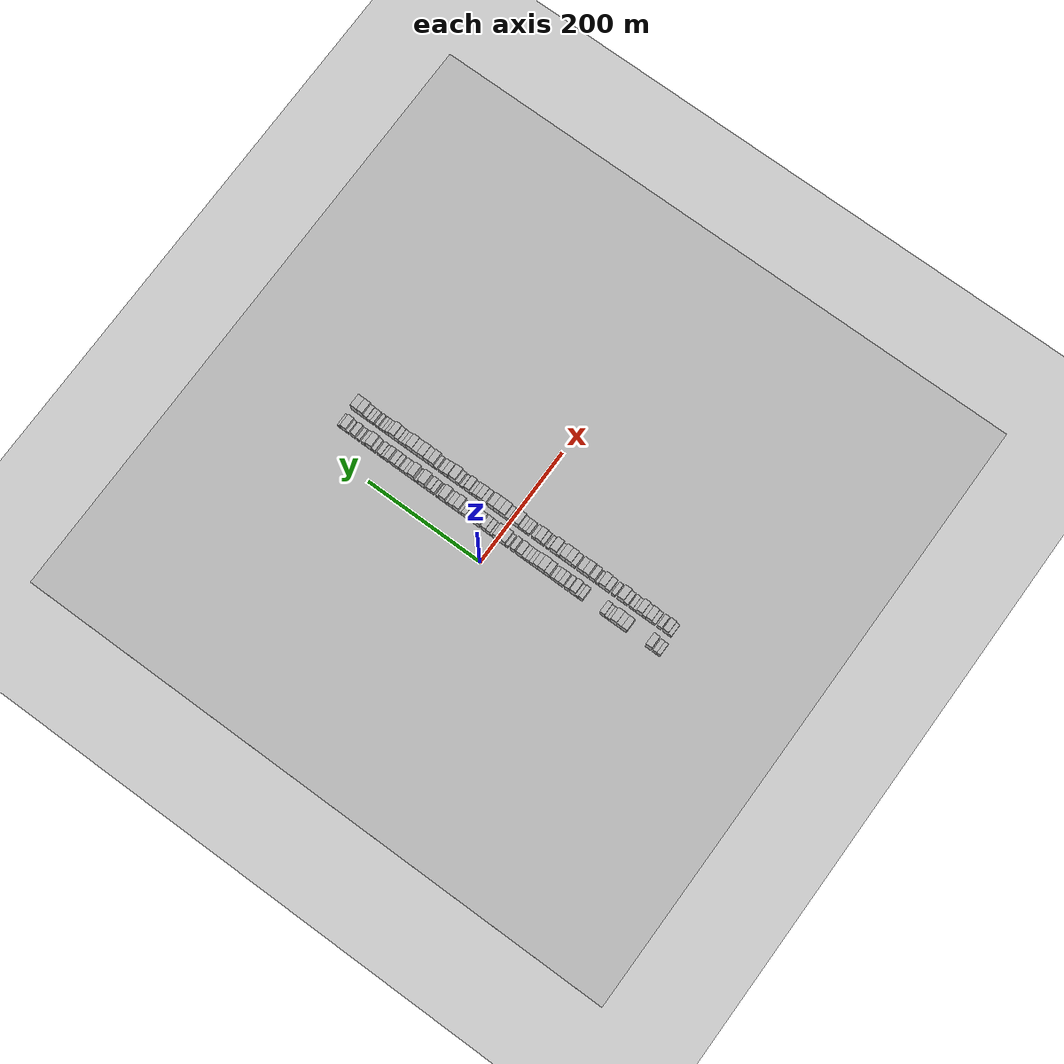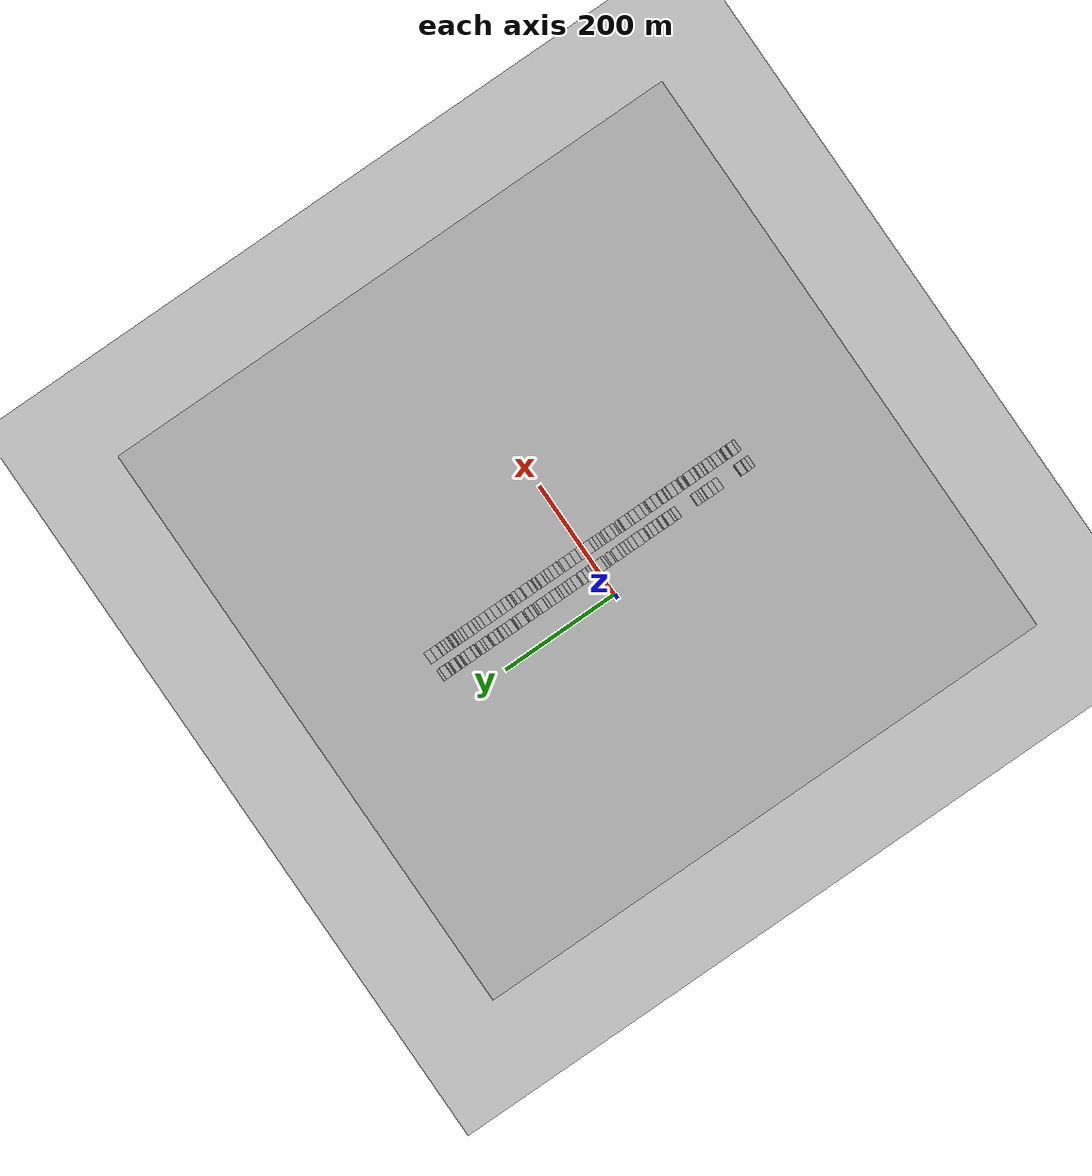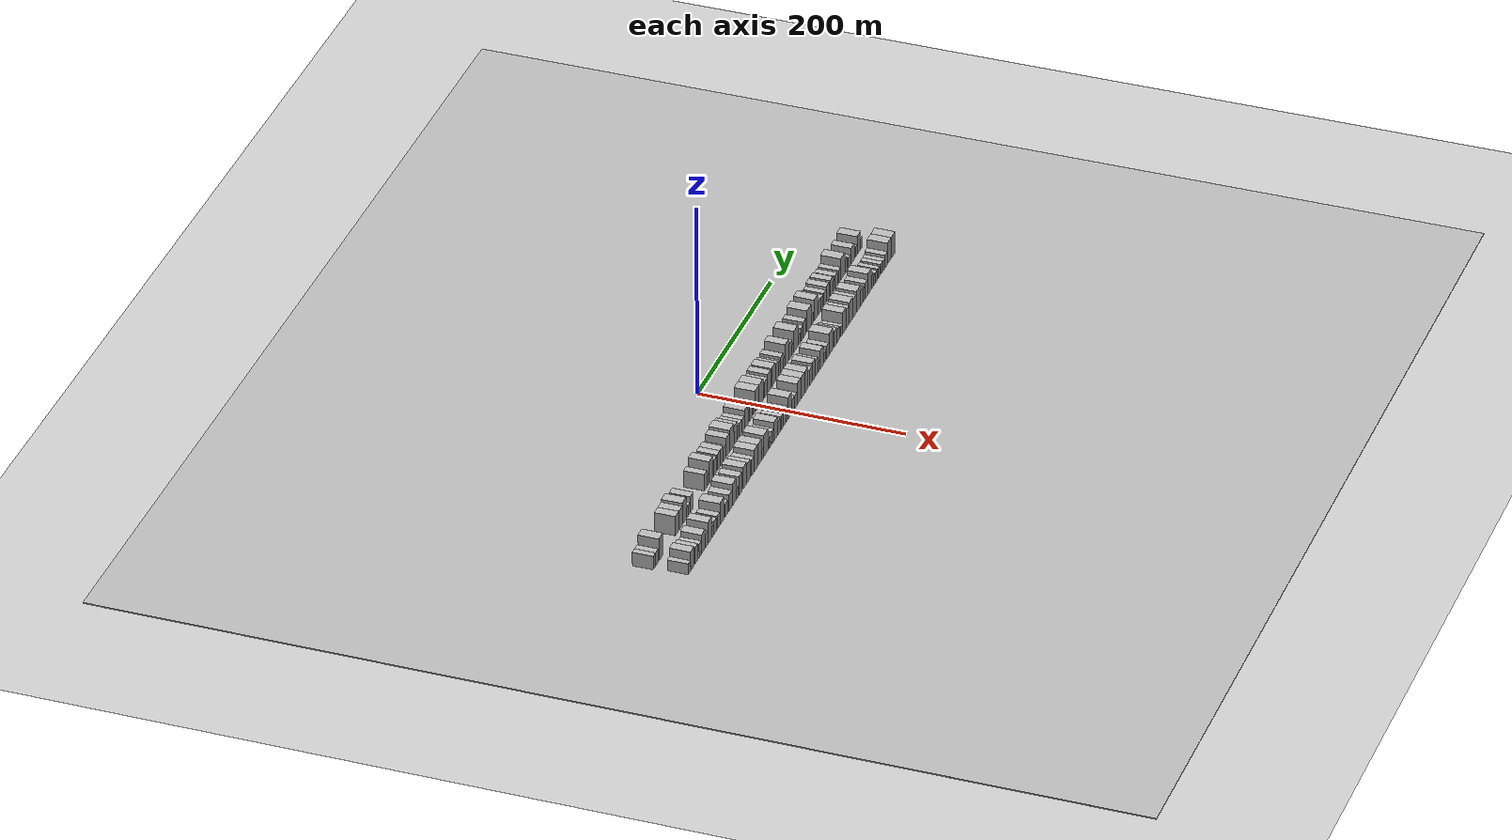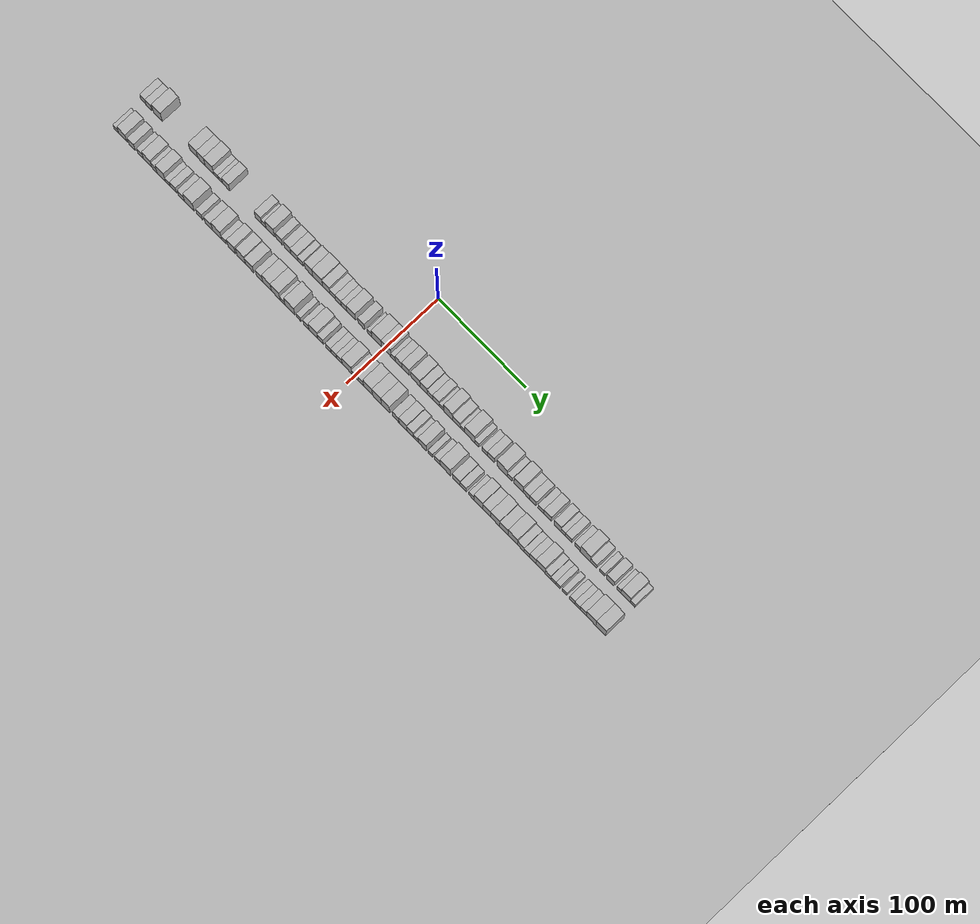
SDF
<?xml version="1.0" encoding="utf-8"?>

<sdf version="1.6">

   <world name="default">

      <gui fullscreen="0">

         <camera name="user_camera">

            <pose>-15 0 4.57585 0 0 0</pose>

            <view_controller>orbit</view_controller>

         </camera>

      </gui>

      <scene>

         <sky>

           <clouds>

             <speed>12</speed>

           </clouds>

         </sky>

         <ambient>0.4 0.4 0.4 1</ambient>

         <background>0.7 0.7 0.7 1</background>

         <shadows>1</shadows>

      </scene>

      <gravity>0 0 -9.8066</gravity>

      <magnetic_field>6e-06 2.3e-05 -4.2e-05</magnetic_field>

      <physics default="0" name="default_physics" type="ode">

         <ode>

            <solver>

               <type>quick</type>

               <iters>10</iters>

               <sor>1.0</sor>

               <use_dynamic_moi_rescaling>0</use_dynamic_moi_rescaling>

            </solver>

            <constraints>

               <cfm>0</cfm>

               <erp>0.2</erp>

               <contact_max_correcting_vel>100</contact_max_correcting_vel>

               <contact_surface_layer>0.001</contact_surface_layer>

            </constraints>

         </ode>

         <max_step_size>0.004</max_step_size>

         <real_time_factor>1</real_time_factor>

         <real_time_update_rate>250</real_time_update_rate>

      </physics>

      <light name="sun" type="directional">

         <cast_shadows>1</cast_shadows>

         <pose>0 0 10 0 0 0</pose>

         <diffuse>0.8 0.8 0.8 1</diffuse>

         <specular>0.2 0.2 0.2 1</specular>

         <attenuation>

            <range>1000</range>

            <constant>0.9</constant>

            <linear>0.01</linear>

            <quadratic>0.001</quadratic>

         </attenuation>

         <direction>-0.5 0.1 -0.9</direction>

      </light>

      <include>

         <name>ground_plane_1</name>

         <uri>model://HANNAS_ground_plane</uri>

         <pose>0 0 0  0 0 0</pose>

      </include>

      <include>

         <name>ground_plane_2</name>

         <uri>model://HANNAS_ground_plane</uri>

         <pose>100 0 0  0 0 0</pose>

      </include>

      <model name="building_1">

         <static>1</static>

         <pose frame="">50.0000 -280.9047 0 0.000000 0.000000 0.000000</pose>

         <link name="link">

            <pose frame="">0 0 7.50 0 0 0</pose>

            <collision name="collision">

               <geometry>

                  <box>

                     <size>20.0000 6.1906 15.0000</size>

                  </box>

               </geometry>

               <max_contacts>10</max_contacts>

               <surface>

                  <contact>

                     <ode/>

                  </contact>

                  <bounce/>

                  <friction>

                     <torsional>

                        <ode/>

                     </torsional>

                     <ode/>

                  </friction>

               </surface>

            </collision>

            <visual name="visual">

               <cast_shadows>0</cast_shadows>

               <geometry>

                  <box>

                     <size>20.0000 6.1906 15.0000</size>

                  </box>

               </geometry>

               <material>

                  <script>

                     <uri>model://HANNAS_wall/materials/scripts</uri>

                     <uri>model://HANNAS_wall/materials/textures</uri>

                     <name>vrc/HANNAS_wall</name>

                  </script>

               </material>

            </visual>

            <self_collide>0</self_collide>

            <enable_wind>0</enable_wind>

            <kinematic>0</kinematic>

         </link>

      </model>

      <model name="building_2">

         <static>1</static>

         <pose frame="">50.0000 -274.4337 0 0.000000 0.000000 0.000000</pose>

         <link name="link">

            <pose frame="">0 0 7.50 0 0 0</pose>

            <collision name="collision">

               <geometry>

                  <box>

                     <size>20.0000 6.7513 15.0000</size>

                  </box>

               </geometry>

               <max_contacts>10</max_contacts>

               <surface>

                  <contact>

                     <ode/>

                  </contact>

                  <bounce/>

                  <friction>

                     <torsional>

                        <ode/>

                     </torsional>

                     <ode/>

                  </friction>

               </surface>

            </collision>

            <visual name="visual">

               <cast_shadows>0</cast_shadows>

               <geometry>

                  <box>

                     <size>20.0000 6.7513 15.0000</size>

                  </box>

               </geometry>

               <material>

                  <script>

                     <uri>model://HANNAS_wall/materials/scripts</uri>

                     <uri>model://HANNAS_wall/materials/textures</uri>

                     <name>vrc/HANNAS_wall</name>

                  </script>

               </material>

            </visual>

            <self_collide>0</self_collide>

            <enable_wind>0</enable_wind>

            <kinematic>0</kinematic>

         </link>

      </model>

      <model name="building_3">

         <static>1</static>

         <pose frame="">50.0000 -263.8113 0 0.000000 0.000000 0.000000</pose>

         <link name="link">

            <pose frame="">0 0 12.00 0 0 0</pose>

            <collision name="collision">

               <geometry>

                  <box>

                     <size>20.0000 10.4937 24.0000</size>

                  </box>

               </geometry>

               <max_contacts>10</max_contacts>

               <surface>

                  <contact>

                     <ode/>

                  </contact>

                  <bounce/>

                  <friction>

                     <torsional>

                        <ode/>

                     </torsional>

                     <ode/>

                  </friction>

               </surface>

            </collision>

            <visual name="visual">

               <cast_shadows>0</cast_shadows>

               <geometry>

                  <box>

                     <size>20.0000 10.4937 24.0000</size>

                  </box>

               </geometry>

               <material>

                  <script>

                     <uri>model://HANNAS_wall/materials/scripts</uri>

                     <uri>model://HANNAS_wall/materials/textures</uri>

                     <name>vrc/HANNAS_wall</name>

                  </script>

               </material>

            </visual>

            <self_collide>0</self_collide>

            <enable_wind>0</enable_wind>

            <kinematic>0</kinematic>

         </link>

      </model>

      <model name="building_4">

         <static>1</static>

         <pose frame="">50.0000 -221.5287 0 0.000000 0.000000 0.000000</pose>

         <link name="link">

            <pose frame="">0 0 10.50 0 0 0</pose>

            <collision name="collision">

               <geometry>

                  <box>

                     <size>20.0000 9.3572 21.0000</size>

                  </box>

               </geometry>

               <max_contacts>10</max_contacts>

               <surface>

                  <contact>

                     <ode/>

                  </contact>

                  <bounce/>

                  <friction>

                     <torsional>

                        <ode/>

                     </torsional>

                     <ode/>

                  </friction>

               </surface>

            </collision>

            <visual name="visual">

               <cast_shadows>0</cast_shadows>

               <geometry>

                  <box>

                     <size>20.0000 9.3572 21.0000</size>

                  </box>

               </geometry>

               <material>

                  <script>

                     <uri>model://HANNAS_wall/materials/scripts</uri>

                     <uri>model://HANNAS_wall/materials/textures</uri>

                     <name>vrc/HANNAS_wall</name>

                  </script>

               </material>

            </visual>

            <self_collide>0</self_collide>

            <enable_wind>0</enable_wind>

            <kinematic>0</kinematic>

         </link>

      </model>

      <model name="building_5">

         <static>1</static>

         <pose frame="">50.0000 -212.5647 0 0.000000 0.000000 0.000000</pose>

         <link name="link">

            <pose frame="">0 0 10.50 0 0 0</pose>

            <collision name="collision">

               <geometry>

                  <box>

                     <size>20.0000 8.5709 21.0000</size>

                  </box>

               </geometry>

               <max_contacts>10</max_contacts>

               <surface>

                  <contact>

                     <ode/>

                  </contact>

                  <bounce/>

                  <friction>

                     <torsional>

                        <ode/>

                     </torsional>

                     <ode/>

                  </friction>

               </surface>

            </collision>

            <visual name="visual">

               <cast_shadows>0</cast_shadows>

               <geometry>

                  <box>

                     <size>20.0000 8.5709 21.0000</size>

                  </box>

               </geometry>

               <material>

                  <script>

                     <uri>model://HANNAS_wall/materials/scripts</uri>

                     <uri>model://HANNAS_wall/materials/textures</uri>

                     <name>vrc/HANNAS_wall</name>

                  </script>

               </material>

            </visual>

            <self_collide>0</self_collide>

            <enable_wind>0</enable_wind>

            <kinematic>0</kinematic>

         </link>

      </model>

      <model name="building_6">

         <static>1</static>

         <pose frame="">50.0000 -203.0101 0 0.000000 0.000000 0.000000</pose>

         <link name="link">

            <pose frame="">0 0 12.00 0 0 0</pose>

            <collision name="collision">

               <geometry>

                  <box>

                     <size>20.0000 10.5382 24.0000</size>

                  </box>

               </geometry>

               <max_contacts>10</max_contacts>

               <surface>

                  <contact>

                     <ode/>

                  </contact>

                  <bounce/>

                  <friction>

                     <torsional>

                        <ode/>

                     </torsional>

                     <ode/>

                  </friction>

               </surface>

            </collision>

            <visual name="visual">

               <cast_shadows>0</cast_shadows>

               <geometry>

                  <box>

                     <size>20.0000 10.5382 24.0000</size>

                  </box>

               </geometry>

               <material>

                  <script>

                     <uri>model://HANNAS_wall/materials/scripts</uri>

                     <uri>model://HANNAS_wall/materials/textures</uri>

                     <name>vrc/HANNAS_wall</name>

                  </script>

               </material>

            </visual>

            <self_collide>0</self_collide>

            <enable_wind>0</enable_wind>

            <kinematic>0</kinematic>

         </link>

      </model>

      <model name="building_7">

         <static>1</static>

         <pose frame="">50.0000 -195.1155 0 0.000000 0.000000 0.000000</pose>

         <link name="link">

            <pose frame="">0 0 6.00 0 0 0</pose>

            <collision name="collision">

               <geometry>

                  <box>

                     <size>20.0000 5.2510 12.0000</size>

                  </box>

               </geometry>

               <max_contacts>10</max_contacts>

               <surface>

                  <contact>

                     <ode/>

                  </contact>

                  <bounce/>

                  <friction>

                     <torsional>

                        <ode/>

                     </torsional>

                     <ode/>

                  </friction>

               </surface>

            </collision>

            <visual name="visual">

               <cast_shadows>0</cast_shadows>

               <geometry>

                  <box>

                     <size>20.0000 5.2510 12.0000</size>

                  </box>

               </geometry>

               <material>

                  <script>

                     <uri>model://HANNAS_wall/materials/scripts</uri>

                     <uri>model://HANNAS_wall/materials/textures</uri>

                     <name>vrc/HANNAS_wall</name>

                  </script>

               </material>

            </visual>

            <self_collide>0</self_collide>

            <enable_wind>0</enable_wind>

            <kinematic>0</kinematic>

         </link>

      </model>

      <model name="building_8">

         <static>1</static>

         <pose frame="">50.0000 -190.0040 0 0.000000 0.000000 0.000000</pose>

         <link name="link">

            <pose frame="">0 0 6.00 0 0 0</pose>

            <collision name="collision">

               <geometry>

                  <box>

                     <size>20.0000 4.9719 12.0000</size>

                  </box>

               </geometry>

               <max_contacts>10</max_contacts>

               <surface>

                  <contact>

                     <ode/>

                  </contact>

                  <bounce/>

                  <friction>

                     <torsional>

                        <ode/>

                     </torsional>

                     <ode/>

                  </friction>

               </surface>

            </collision>

            <visual name="visual">

               <cast_shadows>0</cast_shadows>

               <geometry>

                  <box>

                     <size>20.0000 4.9719 12.0000</size>

                  </box>

               </geometry>

               <material>

                  <script>

                     <uri>model://HANNAS_wall/materials/scripts</uri>

                     <uri>model://HANNAS_wall/materials/textures</uri>

                     <name>vrc/HANNAS_wall</name>

                  </script>

               </material>

            </visual>

            <self_collide>0</self_collide>

            <enable_wind>0</enable_wind>

            <kinematic>0</kinematic>

         </link>

      </model>

      <model name="building_9">

         <static>1</static>

         <pose frame="">50.0000 -183.3172 0 0.000000 0.000000 0.000000</pose>

         <link name="link">

            <pose frame="">0 0 9.00 0 0 0</pose>

            <collision name="collision">

               <geometry>

                  <box>

                     <size>20.0000 8.4017 18.0000</size>

                  </box>

               </geometry>

               <max_contacts>10</max_contacts>

               <surface>

                  <contact>

                     <ode/>

                  </contact>

                  <bounce/>

                  <friction>

                     <torsional>

                        <ode/>

                     </torsional>

                     <ode/>

                  </friction>

               </surface>

            </collision>

            <visual name="visual">

               <cast_shadows>0</cast_shadows>

               <geometry>

                  <box>

                     <size>20.0000 8.4017 18.0000</size>

                  </box>

               </geometry>

               <material>

                  <script>

                     <uri>model://HANNAS_wall/materials/scripts</uri>

                     <uri>model://HANNAS_wall/materials/textures</uri>

                     <name>vrc/HANNAS_wall</name>

                  </script>

               </material>

            </visual>

            <self_collide>0</self_collide>

            <enable_wind>0</enable_wind>

            <kinematic>0</kinematic>

         </link>

      </model>

      <model name="building_10">

         <static>1</static>

         <pose frame="">50.0000 -145.7531 0 0.000000 0.000000 0.000000</pose>

         <link name="link">

            <pose frame="">0 0 9.00 0 0 0</pose>

            <collision name="collision">

               <geometry>

                  <box>

                     <size>20.0000 7.5755 18.0000</size>

                  </box>

               </geometry>

               <max_contacts>10</max_contacts>

               <surface>

                  <contact>

                     <ode/>

                  </contact>

                  <bounce/>

                  <friction>

                     <torsional>

                        <ode/>

                     </torsional>

                     <ode/>

                  </friction>

               </surface>

            </collision>

            <visual name="visual">

               <cast_shadows>0</cast_shadows>

               <geometry>

                  <box>

                     <size>20.0000 7.5755 18.0000</size>

                  </box>

               </geometry>

               <material>

                  <script>

                     <uri>model://HANNAS_wall/materials/scripts</uri>

                     <uri>model://HANNAS_wall/materials/textures</uri>

                     <name>vrc/HANNAS_wall</name>

                  </script>

               </material>

            </visual>

            <self_collide>0</self_collide>

            <enable_wind>0</enable_wind>

            <kinematic>0</kinematic>

         </link>

      </model>

      <model name="building_11">

         <static>1</static>

         <pose frame="">50.0000 -139.3310 0 0.000000 0.000000 0.000000</pose>

         <link name="link">

            <pose frame="">0 0 6.00 0 0 0</pose>

            <collision name="collision">

               <geometry>

                  <box>

                     <size>20.0000 5.2685 12.0000</size>

                  </box>

               </geometry>

               <max_contacts>10</max_contacts>

               <surface>

                  <contact>

                     <ode/>

                  </contact>

                  <bounce/>

                  <friction>

                     <torsional>

                        <ode/>

                     </torsional>

                     <ode/>

                  </friction>

               </surface>

            </collision>

            <visual name="visual">

               <cast_shadows>0</cast_shadows>

               <geometry>

                  <box>

                     <size>20.0000 5.2685 12.0000</size>

                  </box>

               </geometry>

               <material>

                  <script>

                     <uri>model://HANNAS_wall/materials/scripts</uri>

                     <uri>model://HANNAS_wall/materials/textures</uri>

                     <name>vrc/HANNAS_wall</name>

                  </script>

               </material>

            </visual>

            <self_collide>0</self_collide>

            <enable_wind>0</enable_wind>

            <kinematic>0</kinematic>

         </link>

      </model>

      <model name="building_12">

         <static>1</static>

         <pose frame="">50.0000 -131.7397 0 0.000000 0.000000 0.000000</pose>

         <link name="link">

            <pose frame="">0 0 12.00 0 0 0</pose>

            <collision name="collision">

               <geometry>

                  <box>

                     <size>20.0000 9.9141 24.0000</size>

                  </box>

               </geometry>

               <max_contacts>10</max_contacts>

               <surface>

                  <contact>

                     <ode/>

                  </contact>

                  <bounce/>

                  <friction>

                     <torsional>

                        <ode/>

                     </torsional>

                     <ode/>

                  </friction>

               </surface>

            </collision>

            <visual name="visual">

               <cast_shadows>0</cast_shadows>

               <geometry>

                  <box>

                     <size>20.0000 9.9141 24.0000</size>

                  </box>

               </geometry>

               <material>

                  <script>

                     <uri>model://HANNAS_wall/materials/scripts</uri>

                     <uri>model://HANNAS_wall/materials/textures</uri>

                     <name>vrc/HANNAS_wall</name>

                  </script>

               </material>

            </visual>

            <self_collide>0</self_collide>

            <enable_wind>0</enable_wind>

            <kinematic>0</kinematic>

         </link>

      </model>

      <model name="building_13">

         <static>1</static>

         <pose frame="">50.0000 -121.1283 0 0.000000 0.000000 0.000000</pose>

         <link name="link">

            <pose frame="">0 0 9.00 0 0 0</pose>

            <collision name="collision">

               <geometry>

                  <box>

                     <size>20.0000 7.3088 18.0000</size>

                  </box>

               </geometry>

               <max_contacts>10</max_contacts>

               <surface>

                  <contact>

                     <ode/>

                  </contact>

                  <bounce/>

                  <friction>

                     <torsional>

                        <ode/>

                     </torsional>

                     <ode/>

                  </friction>

               </surface>

            </collision>

            <visual name="visual">

               <cast_shadows>0</cast_shadows>

               <geometry>

                  <box>

                     <size>20.0000 7.3088 18.0000</size>

                  </box>

               </geometry>

               <material>

                  <script>

                     <uri>model://HANNAS_wall/materials/scripts</uri>

                     <uri>model://HANNAS_wall/materials/textures</uri>

                     <name>vrc/HANNAS_wall</name>

                  </script>

               </material>

            </visual>

            <self_collide>0</self_collide>

            <enable_wind>0</enable_wind>

            <kinematic>0</kinematic>

         </link>

      </model>

      <model name="building_14">

         <static>1</static>

         <pose frame="">50.0000 -111.5930 0 0.000000 0.000000 0.000000</pose>

         <link name="link">

            <pose frame="">0 0 9.00 0 0 0</pose>

            <collision name="collision">

               <geometry>

                  <box>

                     <size>20.0000 7.7617 18.0000</size>

                  </box>

               </geometry>

               <max_contacts>10</max_contacts>

               <surface>

                  <contact>

                     <ode/>

                  </contact>

                  <bounce/>

                  <friction>

                     <torsional>

                        <ode/>

                     </torsional>

                     <ode/>

                  </friction>

               </surface>

            </collision>

            <visual name="visual">

               <cast_shadows>0</cast_shadows>

               <geometry>

                  <box>

                     <size>20.0000 7.7617 18.0000</size>

                  </box>

               </geometry>

               <material>

                  <script>

                     <uri>model://HANNAS_wall/materials/scripts</uri>

                     <uri>model://HANNAS_wall/materials/textures</uri>

                     <name>vrc/HANNAS_wall</name>

                  </script>

               </material>

            </visual>

            <self_collide>0</self_collide>

            <enable_wind>0</enable_wind>

            <kinematic>0</kinematic>

         </link>

      </model>

      <model name="building_15">

         <static>1</static>

         <pose frame="">50.0000 -103.5192 0 0.000000 0.000000 0.000000</pose>

         <link name="link">

            <pose frame="">0 0 9.00 0 0 0</pose>

            <collision name="collision">

               <geometry>

                  <box>

                     <size>20.0000 8.3860 18.0000</size>

                  </box>

               </geometry>

               <max_contacts>10</max_contacts>

               <surface>

                  <contact>

                     <ode/>

                  </contact>

                  <bounce/>

                  <friction>

                     <torsional>

                        <ode/>

                     </torsional>

                     <ode/>

                  </friction>

               </surface>

            </collision>

            <visual name="visual">

               <cast_shadows>0</cast_shadows>

               <geometry>

                  <box>

                     <size>20.0000 8.3860 18.0000</size>

                  </box>

               </geometry>

               <material>

                  <script>

                     <uri>model://HANNAS_wall/materials/scripts</uri>

                     <uri>model://HANNAS_wall/materials/textures</uri>

                     <name>vrc/HANNAS_wall</name>

                  </script>

               </material>

            </visual>

            <self_collide>0</self_collide>

            <enable_wind>0</enable_wind>

            <kinematic>0</kinematic>

         </link>

      </model>

      <model name="building_16">

         <static>1</static>

         <pose frame="">50.0000 -96.2797 0 0.000000 0.000000 0.000000</pose>

         <link name="link">

            <pose frame="">0 0 7.50 0 0 0</pose>

            <collision name="collision">

               <geometry>

                  <box>

                     <size>20.0000 6.0930 15.0000</size>

                  </box>

               </geometry>

               <max_contacts>10</max_contacts>

               <surface>

                  <contact>

                     <ode/>

                  </contact>

                  <bounce/>

                  <friction>

                     <torsional>

                        <ode/>

                     </torsional>

                     <ode/>

                  </friction>

               </surface>

            </collision>

            <visual name="visual">

               <cast_shadows>0</cast_shadows>

               <geometry>

                  <box>

                     <size>20.0000 6.0930 15.0000</size>

                  </box>

               </geometry>

               <material>

                  <script>

                     <uri>model://HANNAS_wall/materials/scripts</uri>

                     <uri>model://HANNAS_wall/materials/textures</uri>

                     <name>vrc/HANNAS_wall</name>

                  </script>

               </material>

            </visual>

            <self_collide>0</self_collide>

            <enable_wind>0</enable_wind>

            <kinematic>0</kinematic>

         </link>

      </model>

      <model name="building_17">

         <static>1</static>

         <pose frame="">50.0000 -86.7857 0 0.000000 0.000000 0.000000</pose>

         <link name="link">

            <pose frame="">0 0 10.50 0 0 0</pose>

            <collision name="collision">

               <geometry>

                  <box>

                     <size>20.0000 8.8949 21.0000</size>

                  </box>

               </geometry>

               <max_contacts>10</max_contacts>

               <surface>

                  <contact>

                     <ode/>

                  </contact>

                  <bounce/>

                  <friction>

                     <torsional>

                        <ode/>

                     </torsional>

                     <ode/>

                  </friction>

               </surface>

            </collision>

            <visual name="visual">

               <cast_shadows>0</cast_shadows>

               <geometry>

                  <box>

                     <size>20.0000 8.8949 21.0000</size>

                  </box>

               </geometry>

               <material>

                  <script>

                     <uri>model://HANNAS_wall/materials/scripts</uri>

                     <uri>model://HANNAS_wall/materials/textures</uri>

                     <name>vrc/HANNAS_wall</name>

                  </script>

               </material>

            </visual>

            <self_collide>0</self_collide>

            <enable_wind>0</enable_wind>

            <kinematic>0</kinematic>

         </link>

      </model>

      <model name="building_18">

         <static>1</static>

         <pose frame="">50.0000 -76.5486 0 0.000000 0.000000 0.000000</pose>

         <link name="link">

            <pose frame="">0 0 12.00 0 0 0</pose>

            <collision name="collision">

               <geometry>

                  <box>

                     <size>20.0000 11.5792 24.0000</size>

                  </box>

               </geometry>

               <max_contacts>10</max_contacts>

               <surface>

                  <contact>

                     <ode/>

                  </contact>

                  <bounce/>

                  <friction>

                     <torsional>

                        <ode/>

                     </torsional>

                     <ode/>

                  </friction>

               </surface>

            </collision>

            <visual name="visual">

               <cast_shadows>0</cast_shadows>

               <geometry>

                  <box>

                     <size>20.0000 11.5792 24.0000</size>

                  </box>

               </geometry>

               <material>

                  <script>

                     <uri>model://HANNAS_wall/materials/scripts</uri>

                     <uri>model://HANNAS_wall/materials/textures</uri>

                     <name>vrc/HANNAS_wall</name>

                  </script>

               </material>

            </visual>

            <self_collide>0</self_collide>

            <enable_wind>0</enable_wind>

            <kinematic>0</kinematic>

         </link>

      </model>

      <model name="building_19">

         <static>1</static>

         <pose frame="">50.0000 -66.4720 0 0.000000 0.000000 0.000000</pose>

         <link name="link">

            <pose frame="">0 0 10.50 0 0 0</pose>

            <collision name="collision">

               <geometry>

                  <box>

                     <size>20.0000 8.5740 21.0000</size>

                  </box>

               </geometry>

               <max_contacts>10</max_contacts>

               <surface>

                  <contact>

                     <ode/>

                  </contact>

                  <bounce/>

                  <friction>

                     <torsional>

                        <ode/>

                     </torsional>

                     <ode/>

                  </friction>

               </surface>

            </collision>

            <visual name="visual">

               <cast_shadows>0</cast_shadows>

               <geometry>

                  <box>

                     <size>20.0000 8.5740 21.0000</size>

                  </box>

               </geometry>

               <material>

                  <script>

                     <uri>model://HANNAS_wall/materials/scripts</uri>

                     <uri>model://HANNAS_wall/materials/textures</uri>

                     <name>vrc/HANNAS_wall</name>

                  </script>

               </material>

            </visual>

            <self_collide>0</self_collide>

            <enable_wind>0</enable_wind>

            <kinematic>0</kinematic>

         </link>

      </model>

      <model name="building_20">

         <static>1</static>

         <pose frame="">50.0000 -59.0821 0 0.000000 0.000000 0.000000</pose>

         <link name="link">

            <pose frame="">0 0 7.50 0 0 0</pose>

            <collision name="collision">

               <geometry>

                  <box>

                     <size>20.0000 6.2059 15.0000</size>

                  </box>

               </geometry>

               <max_contacts>10</max_contacts>

               <surface>

                  <contact>

                     <ode/>

                  </contact>

                  <bounce/>

                  <friction>

                     <torsional>

                        <ode/>

                     </torsional>

                     <ode/>

                  </friction>

               </surface>

            </collision>

            <visual name="visual">

               <cast_shadows>0</cast_shadows>

               <geometry>

                  <box>

                     <size>20.0000 6.2059 15.0000</size>

                  </box>

               </geometry>

               <material>

                  <script>

                     <uri>model://HANNAS_wall/materials/scripts</uri>

                     <uri>model://HANNAS_wall/materials/textures</uri>

                     <name>vrc/HANNAS_wall</name>

                  </script>

               </material>

            </visual>

            <self_collide>0</self_collide>

            <enable_wind>0</enable_wind>

            <kinematic>0</kinematic>

         </link>

      </model>

      <model name="building_21">

         <static>1</static>

         <pose frame="">50.0000 -52.5241 0 0.000000 0.000000 0.000000</pose>

         <link name="link">

            <pose frame="">0 0 7.50 0 0 0</pose>

            <collision name="collision">

               <geometry>

                  <box>

                     <size>20.0000 6.9101 15.0000</size>

                  </box>

               </geometry>

               <max_contacts>10</max_contacts>

               <surface>

                  <contact>

                     <ode/>

                  </contact>

                  <bounce/>

                  <friction>

                     <torsional>

                        <ode/>

                     </torsional>

                     <ode/>

                  </friction>

               </surface>

            </collision>

            <visual name="visual">

               <cast_shadows>0</cast_shadows>

               <geometry>

                  <box>

                     <size>20.0000 6.9101 15.0000</size>

                  </box>

               </geometry>

               <material>

                  <script>

                     <uri>model://HANNAS_wall/materials/scripts</uri>

                     <uri>model://HANNAS_wall/materials/textures</uri>

                     <name>vrc/HANNAS_wall</name>

                  </script>

               </material>

            </visual>

            <self_collide>0</self_collide>

            <enable_wind>0</enable_wind>

            <kinematic>0</kinematic>

         </link>

      </model>

      <model name="building_22">

         <static>1</static>

         <pose frame="">50.0000 -45.9291 0 0.000000 0.000000 0.000000</pose>

         <link name="link">

            <pose frame="">0 0 7.50 0 0 0</pose>

            <collision name="collision">

               <geometry>

                  <box>

                     <size>20.0000 6.2798 15.0000</size>

                  </box>

               </geometry>

               <max_contacts>10</max_contacts>

               <surface>

                  <contact>

                     <ode/>

                  </contact>

                  <bounce/>

                  <friction>

                     <torsional>

                        <ode/>

                     </torsional>

                     <ode/>

                  </friction>

               </surface>

            </collision>

            <visual name="visual">

               <cast_shadows>0</cast_shadows>

               <geometry>

                  <box>

                     <size>20.0000 6.2798 15.0000</size>

                  </box>

               </geometry>

               <material>

                  <script>

                     <uri>model://HANNAS_wall/materials/scripts</uri>

                     <uri>model://HANNAS_wall/materials/textures</uri>

                     <name>vrc/HANNAS_wall</name>

                  </script>

               </material>

            </visual>

            <self_collide>0</self_collide>

            <enable_wind>0</enable_wind>

            <kinematic>0</kinematic>

         </link>

      </model>

      <model name="building_23">

         <static>1</static>

         <pose frame="">50.0000 -37.7250 0 0.000000 0.000000 0.000000</pose>

         <link name="link">

            <pose frame="">0 0 10.50 0 0 0</pose>

            <collision name="collision">

               <geometry>

                  <box>

                     <size>20.0000 10.1284 21.0000</size>

                  </box>

               </geometry>

               <max_contacts>10</max_contacts>

               <surface>

                  <contact>

                     <ode/>

                  </contact>

                  <bounce/>

                  <friction>

                     <torsional>

                        <ode/>

                     </torsional>

                     <ode/>

                  </friction>

               </surface>

            </collision>

            <visual name="visual">

               <cast_shadows>0</cast_shadows>

               <geometry>

                  <box>

                     <size>20.0000 10.1284 21.0000</size>

                  </box>

               </geometry>

               <material>

                  <script>

                     <uri>model://HANNAS_wall/materials/scripts</uri>

                     <uri>model://HANNAS_wall/materials/textures</uri>

                     <name>vrc/HANNAS_wall</name>

                  </script>

               </material>

            </visual>

            <self_collide>0</self_collide>

            <enable_wind>0</enable_wind>

            <kinematic>0</kinematic>

         </link>

      </model>

      <model name="building_24">

         <static>1</static>

         <pose frame="">50.0000 -25.8488 0 0.000000 0.000000 0.000000</pose>

         <link name="link">

            <pose frame="">0 0 9.00 0 0 0</pose>

            <collision name="collision">

               <geometry>

                  <box>

                     <size>20.0000 7.6238 18.0000</size>

                  </box>

               </geometry>

               <max_contacts>10</max_contacts>

               <surface>

                  <contact>

                     <ode/>

                  </contact>

                  <bounce/>

                  <friction>

                     <torsional>

                        <ode/>

                     </torsional>

                     <ode/>

                  </friction>

               </surface>

            </collision>

            <visual name="visual">

               <cast_shadows>0</cast_shadows>

               <geometry>

                  <box>

                     <size>20.0000 7.6238 18.0000</size>

                  </box>

               </geometry>

               <material>

                  <script>

                     <uri>model://HANNAS_wall/materials/scripts</uri>

                     <uri>model://HANNAS_wall/materials/textures</uri>

                     <name>vrc/HANNAS_wall</name>

                  </script>

               </material>

            </visual>

            <self_collide>0</self_collide>

            <enable_wind>0</enable_wind>

            <kinematic>0</kinematic>

         </link>

      </model>

      <model name="building_25">

         <static>1</static>

         <pose frame="">50.0000 -16.4413 0 0.000000 0.000000 0.000000</pose>

         <link name="link">

            <pose frame="">0 0 6.00 0 0 0</pose>

            <collision name="collision">

               <geometry>

                  <box>

                     <size>20.0000 5.1911 12.0000</size>

                  </box>

               </geometry>

               <max_contacts>10</max_contacts>

               <surface>

                  <contact>

                     <ode/>

                  </contact>

                  <bounce/>

                  <friction>

                     <torsional>

                        <ode/>

                     </torsional>

                     <ode/>

                  </friction>

               </surface>

            </collision>

            <visual name="visual">

               <cast_shadows>0</cast_shadows>

               <geometry>

                  <box>

                     <size>20.0000 5.1911 12.0000</size>

                  </box>

               </geometry>

               <material>

                  <script>

                     <uri>model://HANNAS_wall/materials/scripts</uri>

                     <uri>model://HANNAS_wall/materials/textures</uri>

                     <name>vrc/HANNAS_wall</name>

                  </script>

               </material>

            </visual>

            <self_collide>0</self_collide>

            <enable_wind>0</enable_wind>

            <kinematic>0</kinematic>

         </link>

      </model>

      <model name="building_26">

         <static>1</static>

         <pose frame="">50.0000 -8.2512 0 0.000000 0.000000 0.000000</pose>

         <link name="link">

            <pose frame="">0 0 12.00 0 0 0</pose>

            <collision name="collision">

               <geometry>

                  <box>

                     <size>20.0000 11.1893 24.0000</size>

                  </box>

               </geometry>

               <max_contacts>10</max_contacts>

               <surface>

                  <contact>

                     <ode/>

                  </contact>

                  <bounce/>

                  <friction>

                     <torsional>

                        <ode/>

                     </torsional>

                     <ode/>

                  </friction>

               </surface>

            </collision>

            <visual name="visual">

               <cast_shadows>0</cast_shadows>

               <geometry>

                  <box>

                     <size>20.0000 11.1893 24.0000</size>

                  </box>

               </geometry>

               <material>

                  <script>

                     <uri>model://HANNAS_wall/materials/scripts</uri>

                     <uri>model://HANNAS_wall/materials/textures</uri>

                     <name>vrc/HANNAS_wall</name>

                  </script>

               </material>

            </visual>

            <self_collide>0</self_collide>

            <enable_wind>0</enable_wind>

            <kinematic>0</kinematic>

         </link>

      </model>

      <model name="building_27">

         <static>1</static>

         <pose frame="">50.0000 2.8335 0 0.000000 0.000000 0.000000</pose>

         <link name="link">

            <pose frame="">0 0 12.00 0 0 0</pose>

            <collision name="collision">

               <geometry>

                  <box>

                     <size>20.0000 10.9800 24.0000</size>

                  </box>

               </geometry>

               <max_contacts>10</max_contacts>

               <surface>

                  <contact>

                     <ode/>

                  </contact>

                  <bounce/>

                  <friction>

                     <torsional>

                        <ode/>

                     </torsional>

                     <ode/>

                  </friction>

               </surface>

            </collision>

            <visual name="visual">

               <cast_shadows>0</cast_shadows>

               <geometry>

                  <box>

                     <size>20.0000 10.9800 24.0000</size>

                  </box>

               </geometry>

               <material>

                  <script>

                     <uri>model://HANNAS_wall/materials/scripts</uri>

                     <uri>model://HANNAS_wall/materials/textures</uri>

                     <name>vrc/HANNAS_wall</name>

                  </script>

               </material>

            </visual>

            <self_collide>0</self_collide>

            <enable_wind>0</enable_wind>

            <kinematic>0</kinematic>

         </link>

      </model>

      <model name="building_28">

         <static>1</static>

         <pose frame="">50.0000 10.7881 0 0.000000 0.000000 0.000000</pose>

         <link name="link">

            <pose frame="">0 0 6.00 0 0 0</pose>

            <collision name="collision">

               <geometry>

                  <box>

                     <size>20.0000 4.9293 12.0000</size>

                  </box>

               </geometry>

               <max_contacts>10</max_contacts>

               <surface>

                  <contact>

                     <ode/>

                  </contact>

                  <bounce/>

                  <friction>

                     <torsional>

                        <ode/>

                     </torsional>

                     <ode/>

                  </friction>

               </surface>

            </collision>

            <visual name="visual">

               <cast_shadows>0</cast_shadows>

               <geometry>

                  <box>

                     <size>20.0000 4.9293 12.0000</size>

                  </box>

               </geometry>

               <material>

                  <script>

                     <uri>model://HANNAS_wall/materials/scripts</uri>

                     <uri>model://HANNAS_wall/materials/textures</uri>

                     <name>vrc/HANNAS_wall</name>

                  </script>

               </material>

            </visual>

            <self_collide>0</self_collide>

            <enable_wind>0</enable_wind>

            <kinematic>0</kinematic>

         </link>

      </model>

      <model name="building_29">

         <static>1</static>

         <pose frame="">50.0000 17.0681 0 0.000000 0.000000 0.000000</pose>

         <link name="link">

            <pose frame="">0 0 9.00 0 0 0</pose>

            <collision name="collision">

               <geometry>

                  <box>

                     <size>20.0000 7.6307 18.0000</size>

                  </box>

               </geometry>

               <max_contacts>10</max_contacts>

               <surface>

                  <contact>

                     <ode/>

                  </contact>

                  <bounce/>

                  <friction>

                     <torsional>

                        <ode/>

                     </torsional>

                     <ode/>

                  </friction>

               </surface>

            </collision>

            <visual name="visual">

               <cast_shadows>0</cast_shadows>

               <geometry>

                  <box>

                     <size>20.0000 7.6307 18.0000</size>

                  </box>

               </geometry>

               <material>

                  <script>

                     <uri>model://HANNAS_wall/materials/scripts</uri>

                     <uri>model://HANNAS_wall/materials/textures</uri>

                     <name>vrc/HANNAS_wall</name>

                  </script>

               </material>

            </visual>

            <self_collide>0</self_collide>

            <enable_wind>0</enable_wind>

            <kinematic>0</kinematic>

         </link>

      </model>

      <model name="building_30">

         <static>1</static>

         <pose frame="">50.0000 25.1394 0 0.000000 0.000000 0.000000</pose>

         <link name="link">

            <pose frame="">0 0 10.50 0 0 0</pose>

            <collision name="collision">

               <geometry>

                  <box>

                     <size>20.0000 8.5120 21.0000</size>

                  </box>

               </geometry>

               <max_contacts>10</max_contacts>

               <surface>

                  <contact>

                     <ode/>

                  </contact>

                  <bounce/>

                  <friction>

                     <torsional>

                        <ode/>

                     </torsional>

                     <ode/>

                  </friction>

               </surface>

            </collision>

            <visual name="visual">

               <cast_shadows>0</cast_shadows>

               <geometry>

                  <box>

                     <size>20.0000 8.5120 21.0000</size>

                  </box>

               </geometry>

               <material>

                  <script>

                     <uri>model://HANNAS_wall/materials/scripts</uri>

                     <uri>model://HANNAS_wall/materials/textures</uri>

                     <name>vrc/HANNAS_wall</name>

                  </script>

               </material>

            </visual>

            <self_collide>0</self_collide>

            <enable_wind>0</enable_wind>

            <kinematic>0</kinematic>

         </link>

      </model>

      <model name="building_31">

         <static>1</static>

         <pose frame="">50.0000 36.5549 0 0.000000 0.000000 0.000000</pose>

         <link name="link">

            <pose frame="">0 0 10.50 0 0 0</pose>

            <collision name="collision">

               <geometry>

                  <box>

                     <size>20.0000 10.3190 21.0000</size>

                  </box>

               </geometry>

               <max_contacts>10</max_contacts>

               <surface>

                  <contact>

                     <ode/>

                  </contact>

                  <bounce/>

                  <friction>

                     <torsional>

                        <ode/>

                     </torsional>

                     <ode/>

                  </friction>

               </surface>

            </collision>

            <visual name="visual">

               <cast_shadows>0</cast_shadows>

               <geometry>

                  <box>

                     <size>20.0000 10.3190 21.0000</size>

                  </box>

               </geometry>

               <material>

                  <script>

                     <uri>model://HANNAS_wall/materials/scripts</uri>

                     <uri>model://HANNAS_wall/materials/textures</uri>

                     <name>vrc/HANNAS_wall</name>

                  </script>

               </material>

            </visual>

            <self_collide>0</self_collide>

            <enable_wind>0</enable_wind>

            <kinematic>0</kinematic>

         </link>

      </model>

      <model name="building_32">

         <static>1</static>

         <pose frame="">50.0000 45.7655 0 0.000000 0.000000 0.000000</pose>

         <link name="link">

            <pose frame="">0 0 9.00 0 0 0</pose>

            <collision name="collision">

               <geometry>

                  <box>

                     <size>20.0000 8.1023 18.0000</size>

                  </box>

               </geometry>

               <max_contacts>10</max_contacts>

               <surface>

                  <contact>

                     <ode/>

                  </contact>

                  <bounce/>

                  <friction>

                     <torsional>

                        <ode/>

                     </torsional>

                     <ode/>

                  </friction>

               </surface>

            </collision>

            <visual name="visual">

               <cast_shadows>0</cast_shadows>

               <geometry>

                  <box>

                     <size>20.0000 8.1023 18.0000</size>

                  </box>

               </geometry>

               <material>

                  <script>

                     <uri>model://HANNAS_wall/materials/scripts</uri>

                     <uri>model://HANNAS_wall/materials/textures</uri>

                     <name>vrc/HANNAS_wall</name>

                  </script>

               </material>

            </visual>

            <self_collide>0</self_collide>

            <enable_wind>0</enable_wind>

            <kinematic>0</kinematic>

         </link>

      </model>

      <model name="building_33">

         <static>1</static>

         <pose frame="">50.0000 53.0973 0 0.000000 0.000000 0.000000</pose>

         <link name="link">

            <pose frame="">0 0 7.50 0 0 0</pose>

            <collision name="collision">

               <geometry>

                  <box>

                     <size>20.0000 6.5614 15.0000</size>

                  </box>

               </geometry>

               <max_contacts>10</max_contacts>

               <surface>

                  <contact>

                     <ode/>

                  </contact>

                  <bounce/>

                  <friction>

                     <torsional>

                        <ode/>

                     </torsional>

                     <ode/>

                  </friction>

               </surface>

            </collision>

            <visual name="visual">

               <cast_shadows>0</cast_shadows>

               <geometry>

                  <box>

                     <size>20.0000 6.5614 15.0000</size>

                  </box>

               </geometry>

               <material>

                  <script>

                     <uri>model://HANNAS_wall/materials/scripts</uri>

                     <uri>model://HANNAS_wall/materials/textures</uri>

                     <name>vrc/HANNAS_wall</name>

                  </script>

               </material>

            </visual>

            <self_collide>0</self_collide>

            <enable_wind>0</enable_wind>

            <kinematic>0</kinematic>

         </link>

      </model>

      <model name="building_34">

         <static>1</static>

         <pose frame="">50.0000 60.1738 0 0.000000 0.000000 0.000000</pose>

         <link name="link">

            <pose frame="">0 0 9.00 0 0 0</pose>

            <collision name="collision">

               <geometry>

                  <box>

                     <size>20.0000 7.5915 18.0000</size>

                  </box>

               </geometry>

               <max_contacts>10</max_contacts>

               <surface>

                  <contact>

                     <ode/>

                  </contact>

                  <bounce/>

                  <friction>

                     <torsional>

                        <ode/>

                     </torsional>

                     <ode/>

                  </friction>

               </surface>

            </collision>

            <visual name="visual">

               <cast_shadows>0</cast_shadows>

               <geometry>

                  <box>

                     <size>20.0000 7.5915 18.0000</size>

                  </box>

               </geometry>

               <material>

                  <script>

                     <uri>model://HANNAS_wall/materials/scripts</uri>

                     <uri>model://HANNAS_wall/materials/textures</uri>

                     <name>vrc/HANNAS_wall</name>

                  </script>

               </material>

            </visual>

            <self_collide>0</self_collide>

            <enable_wind>0</enable_wind>

            <kinematic>0</kinematic>

         </link>

      </model>

      <model name="building_35">

         <static>1</static>

         <pose frame="">50.0000 66.4325 0 0.000000 0.000000 0.000000</pose>

         <link name="link">

            <pose frame="">0 0 6.00 0 0 0</pose>

            <collision name="collision">

               <geometry>

                  <box>

                     <size>20.0000 4.9259 12.0000</size>

                  </box>

               </geometry>

               <max_contacts>10</max_contacts>

               <surface>

                  <contact>

                     <ode/>

                  </contact>

                  <bounce/>

                  <friction>

                     <torsional>

                        <ode/>

                     </torsional>

                     <ode/>

                  </friction>

               </surface>

            </collision>

            <visual name="visual">

               <cast_shadows>0</cast_shadows>

               <geometry>

                  <box>

                     <size>20.0000 4.9259 12.0000</size>

                  </box>

               </geometry>

               <material>

                  <script>

                     <uri>model://HANNAS_wall/materials/scripts</uri>

                     <uri>model://HANNAS_wall/materials/textures</uri>

                     <name>vrc/HANNAS_wall</name>

                  </script>

               </material>

            </visual>

            <self_collide>0</self_collide>

            <enable_wind>0</enable_wind>

            <kinematic>0</kinematic>

         </link>

      </model>

      <model name="building_36">

         <static>1</static>

         <pose frame="">50.0000 73.8627 0 0.000000 0.000000 0.000000</pose>

         <link name="link">

            <pose frame="">0 0 12.00 0 0 0</pose>

            <collision name="collision">

               <geometry>

                  <box>

                     <size>20.0000 9.9345 24.0000</size>

                  </box>

               </geometry>

               <max_contacts>10</max_contacts>

               <surface>

                  <contact>

                     <ode/>

                  </contact>

                  <bounce/>

                  <friction>

                     <torsional>

                        <ode/>

                     </torsional>

                     <ode/>

                  </friction>

               </surface>

            </collision>

            <visual name="visual">

               <cast_shadows>0</cast_shadows>

               <geometry>

                  <box>

                     <size>20.0000 9.9345 24.0000</size>

                  </box>

               </geometry>

               <material>

                  <script>

                     <uri>model://HANNAS_wall/materials/scripts</uri>

                     <uri>model://HANNAS_wall/materials/textures</uri>

                     <name>vrc/HANNAS_wall</name>

                  </script>

               </material>

            </visual>

            <self_collide>0</self_collide>

            <enable_wind>0</enable_wind>

            <kinematic>0</kinematic>

         </link>

      </model>

      <model name="building_37">

         <static>1</static>

         <pose frame="">50.0000 83.3168 0 0.000000 0.000000 0.000000</pose>

         <link name="link">

            <pose frame="">0 0 9.00 0 0 0</pose>

            <collision name="collision">

               <geometry>

                  <box>

                     <size>20.0000 8.9738 18.0000</size>

                  </box>

               </geometry>

               <max_contacts>10</max_contacts>

               <surface>

                  <contact>

                     <ode/>

                  </contact>

                  <bounce/>

                  <friction>

                     <torsional>

                        <ode/>

                     </torsional>

                     <ode/>

                  </friction>

               </surface>

            </collision>

            <visual name="visual">

               <cast_shadows>0</cast_shadows>

               <geometry>

                  <box>

                     <size>20.0000 8.9738 18.0000</size>

                  </box>

               </geometry>

               <material>

                  <script>

                     <uri>model://HANNAS_wall/materials/scripts</uri>

                     <uri>model://HANNAS_wall/materials/textures</uri>

                     <name>vrc/HANNAS_wall</name>

                  </script>

               </material>

            </visual>

            <self_collide>0</self_collide>

            <enable_wind>0</enable_wind>

            <kinematic>0</kinematic>

         </link>

      </model>

      <model name="building_38">

         <static>1</static>

         <pose frame="">50.0000 90.3598 0 0.000000 0.000000 0.000000</pose>

         <link name="link">

            <pose frame="">0 0 6.00 0 0 0</pose>

            <collision name="collision">

               <geometry>

                  <box>

                     <size>20.0000 5.1121 12.0000</size>

                  </box>

               </geometry>

               <max_contacts>10</max_contacts>

               <surface>

                  <contact>

                     <ode/>

                  </contact>

                  <bounce/>

                  <friction>

                     <torsional>

                        <ode/>

                     </torsional>

                     <ode/>

                  </friction>

               </surface>

            </collision>

            <visual name="visual">

               <cast_shadows>0</cast_shadows>

               <geometry>

                  <box>

                     <size>20.0000 5.1121 12.0000</size>

                  </box>

               </geometry>

               <material>

                  <script>

                     <uri>model://HANNAS_wall/materials/scripts</uri>

                     <uri>model://HANNAS_wall/materials/textures</uri>

                     <name>vrc/HANNAS_wall</name>

                  </script>

               </material>

            </visual>

            <self_collide>0</self_collide>

            <enable_wind>0</enable_wind>

            <kinematic>0</kinematic>

         </link>

      </model>

      <model name="building_39">

         <static>1</static>

         <pose frame="">50.0000 98.5224 0 0.000000 0.000000 0.000000</pose>

         <link name="link">

            <pose frame="">0 0 12.00 0 0 0</pose>

            <collision name="collision">

               <geometry>

                  <box>

                     <size>20.0000 11.2131 24.0000</size>

                  </box>

               </geometry>

               <max_contacts>10</max_contacts>

               <surface>

                  <contact>

                     <ode/>

                  </contact>

                  <bounce/>

                  <friction>

                     <torsional>

                        <ode/>

                     </torsional>

                     <ode/>

                  </friction>

               </surface>

            </collision>

            <visual name="visual">

               <cast_shadows>0</cast_shadows>

               <geometry>

                  <box>

                     <size>20.0000 11.2131 24.0000</size>

                  </box>

               </geometry>

               <material>

                  <script>

                     <uri>model://HANNAS_wall/materials/scripts</uri>

                     <uri>model://HANNAS_wall/materials/textures</uri>

                     <name>vrc/HANNAS_wall</name>

                  </script>

               </material>

            </visual>

            <self_collide>0</self_collide>

            <enable_wind>0</enable_wind>

            <kinematic>0</kinematic>

         </link>

      </model>

      <model name="building_40">

         <static>1</static>

         <pose frame="">50.0000 106.6938 0 0.000000 0.000000 0.000000</pose>

         <link name="link">

            <pose frame="">0 0 6.00 0 0 0</pose>

            <collision name="collision">

               <geometry>

                  <box>

                     <size>20.0000 5.1296 12.0000</size>

                  </box>

               </geometry>

               <max_contacts>10</max_contacts>

               <surface>

                  <contact>

                     <ode/>

                  </contact>

                  <bounce/>

                  <friction>

                     <torsional>

                        <ode/>

                     </torsional>

                     <ode/>

                  </friction>

               </surface>

            </collision>

            <visual name="visual">

               <cast_shadows>0</cast_shadows>

               <geometry>

                  <box>

                     <size>20.0000 5.1296 12.0000</size>

                  </box>

               </geometry>

               <material>

                  <script>

                     <uri>model://HANNAS_wall/materials/scripts</uri>

                     <uri>model://HANNAS_wall/materials/textures</uri>

                     <name>vrc/HANNAS_wall</name>

                  </script>

               </material>

            </visual>

            <self_collide>0</self_collide>

            <enable_wind>0</enable_wind>

            <kinematic>0</kinematic>

         </link>

      </model>

      <model name="building_41">

         <static>1</static>

         <pose frame="">50.0000 115.6049 0 0.000000 0.000000 0.000000</pose>

         <link name="link">

            <pose frame="">0 0 7.50 0 0 0</pose>

            <collision name="collision">

               <geometry>

                  <box>

                     <size>20.0000 6.6927 15.0000</size>

                  </box>

               </geometry>

               <max_contacts>10</max_contacts>

               <surface>

                  <contact>

                     <ode/>

                  </contact>

                  <bounce/>

                  <friction>

                     <torsional>

                        <ode/>

                     </torsional>

                     <ode/>

                  </friction>

               </surface>

            </collision>

            <visual name="visual">

               <cast_shadows>0</cast_shadows>

               <geometry>

                  <box>

                     <size>20.0000 6.6927 15.0000</size>

                  </box>

               </geometry>

               <material>

                  <script>

                     <uri>model://HANNAS_wall/materials/scripts</uri>

                     <uri>model://HANNAS_wall/materials/textures</uri>

                     <name>vrc/HANNAS_wall</name>

                  </script>

               </material>

            </visual>

            <self_collide>0</self_collide>

            <enable_wind>0</enable_wind>

            <kinematic>0</kinematic>

         </link>

      </model>

      <model name="building_42">

         <static>1</static>

         <pose frame="">50.0000 122.7920 0 0.000000 0.000000 0.000000</pose>

         <link name="link">

            <pose frame="">0 0 9.00 0 0 0</pose>

            <collision name="collision">

               <geometry>

                  <box>

                     <size>20.0000 7.6814 18.0000</size>

                  </box>

               </geometry>

               <max_contacts>10</max_contacts>

               <surface>

                  <contact>

                     <ode/>

                  </contact>

                  <bounce/>

                  <friction>

                     <torsional>

                        <ode/>

                     </torsional>

                     <ode/>

                  </friction>

               </surface>

            </collision>

            <visual name="visual">

               <cast_shadows>0</cast_shadows>

               <geometry>

                  <box>

                     <size>20.0000 7.6814 18.0000</size>

                  </box>

               </geometry>

               <material>

                  <script>

                     <uri>model://HANNAS_wall/materials/scripts</uri>

                     <uri>model://HANNAS_wall/materials/textures</uri>

                     <name>vrc/HANNAS_wall</name>

                  </script>

               </material>

            </visual>

            <self_collide>0</self_collide>

            <enable_wind>0</enable_wind>

            <kinematic>0</kinematic>

         </link>

      </model>

      <model name="building_43">

         <static>1</static>

         <pose frame="">50.0000 135.5515 0 0.000000 0.000000 0.000000</pose>

         <link name="link">

            <pose frame="">0 0 12.00 0 0 0</pose>

            <collision name="collision">

               <geometry>

                  <box>

                     <size>20.0000 11.8377 24.0000</size>

                  </box>

               </geometry>

               <max_contacts>10</max_contacts>

               <surface>

                  <contact>

                     <ode/>

                  </contact>

                  <bounce/>

                  <friction>

                     <torsional>

                        <ode/>

                     </torsional>

                     <ode/>

                  </friction>

               </surface>

            </collision>

            <visual name="visual">

               <cast_shadows>0</cast_shadows>

               <geometry>

                  <box>

                     <size>20.0000 11.8377 24.0000</size>

                  </box>

               </geometry>

               <material>

                  <script>

                     <uri>model://HANNAS_wall/materials/scripts</uri>

                     <uri>model://HANNAS_wall/materials/textures</uri>

                     <name>vrc/HANNAS_wall</name>

                  </script>

               </material>

            </visual>

            <self_collide>0</self_collide>

            <enable_wind>0</enable_wind>

            <kinematic>0</kinematic>

         </link>

      </model>

      <model name="building_44">

         <static>1</static>

         <pose frame="">50.0000 144.2986 0 0.000000 0.000000 0.000000</pose>

         <link name="link">

            <pose frame="">0 0 6.00 0 0 0</pose>

            <collision name="collision">

               <geometry>

                  <box>

                     <size>20.0000 5.6564 12.0000</size>

                  </box>

               </geometry>

               <max_contacts>10</max_contacts>

               <surface>

                  <contact>

                     <ode/>

                  </contact>

                  <bounce/>

                  <friction>

                     <torsional>

                        <ode/>

                     </torsional>

                     <ode/>

                  </friction>

               </surface>

            </collision>

            <visual name="visual">

               <cast_shadows>0</cast_shadows>

               <geometry>

                  <box>

                     <size>20.0000 5.6564 12.0000</size>

                  </box>

               </geometry>

               <material>

                  <script>

                     <uri>model://HANNAS_wall/materials/scripts</uri>

                     <uri>model://HANNAS_wall/materials/textures</uri>

                     <name>vrc/HANNAS_wall</name>

                  </script>

               </material>

            </visual>

            <self_collide>0</self_collide>

            <enable_wind>0</enable_wind>

            <kinematic>0</kinematic>

         </link>

      </model>

      <model name="building_45">

         <static>1</static>

         <pose frame="">50.0000 154.3961 0 0.000000 0.000000 0.000000</pose>

         <link name="link">

            <pose frame="">0 0 12.00 0 0 0</pose>

            <collision name="collision">

               <geometry>

                  <box>

                     <size>20.0000 10.5387 24.0000</size>

                  </box>

               </geometry>

               <max_contacts>10</max_contacts>

               <surface>

                  <contact>

                     <ode/>

                  </contact>

                  <bounce/>

                  <friction>

                     <torsional>

                        <ode/>

                     </torsional>

                     <ode/>

                  </friction>

               </surface>

            </collision>

            <visual name="visual">

               <cast_shadows>0</cast_shadows>

               <geometry>

                  <box>

                     <size>20.0000 10.5387 24.0000</size>

                  </box>

               </geometry>

               <material>

                  <script>

                     <uri>model://HANNAS_wall/materials/scripts</uri>

                     <uri>model://HANNAS_wall/materials/textures</uri>

                     <name>vrc/HANNAS_wall</name>

                  </script>

               </material>

            </visual>

            <self_collide>0</self_collide>

            <enable_wind>0</enable_wind>

            <kinematic>0</kinematic>

         </link>

      </model>

      <model name="building_46">

         <static>1</static>

         <pose frame="">50.0000 163.2297 0 0.000000 0.000000 0.000000</pose>

         <link name="link">

            <pose frame="">0 0 7.50 0 0 0</pose>

            <collision name="collision">

               <geometry>

                  <box>

                     <size>20.0000 7.1285 15.0000</size>

                  </box>

               </geometry>

               <max_contacts>10</max_contacts>

               <surface>

                  <contact>

                     <ode/>

                  </contact>

                  <bounce/>

                  <friction>

                     <torsional>

                        <ode/>

                     </torsional>

                     <ode/>

                  </friction>

               </surface>

            </collision>

            <visual name="visual">

               <cast_shadows>0</cast_shadows>

               <geometry>

                  <box>

                     <size>20.0000 7.1285 15.0000</size>

                  </box>

               </geometry>

               <material>

                  <script>

                     <uri>model://HANNAS_wall/materials/scripts</uri>

                     <uri>model://HANNAS_wall/materials/textures</uri>

                     <name>vrc/HANNAS_wall</name>

                  </script>

               </material>

            </visual>

            <self_collide>0</self_collide>

            <enable_wind>0</enable_wind>

            <kinematic>0</kinematic>

         </link>

      </model>

      <model name="building_47">

         <static>1</static>

         <pose frame="">50.0000 170.4870 0 0.000000 0.000000 0.000000</pose>

         <link name="link">

            <pose frame="">0 0 7.50 0 0 0</pose>

            <collision name="collision">

               <geometry>

                  <box>

                     <size>20.0000 7.3861 15.0000</size>

                  </box>

               </geometry>

               <max_contacts>10</max_contacts>

               <surface>

                  <contact>

                     <ode/>

                  </contact>

                  <bounce/>

                  <friction>

                     <torsional>

                        <ode/>

                     </torsional>

                     <ode/>

                  </friction>

               </surface>

            </collision>

            <visual name="visual">

               <cast_shadows>0</cast_shadows>

               <geometry>

                  <box>

                     <size>20.0000 7.3861 15.0000</size>

                  </box>

               </geometry>

               <material>

                  <script>

                     <uri>model://HANNAS_wall/materials/scripts</uri>

                     <uri>model://HANNAS_wall/materials/textures</uri>

                     <name>vrc/HANNAS_wall</name>

                  </script>

               </material>

            </visual>

            <self_collide>0</self_collide>

            <enable_wind>0</enable_wind>

            <kinematic>0</kinematic>

         </link>

      </model>

      <model name="building_48">

         <static>1</static>

         <pose frame="">50.0000 179.4662 0 0.000000 0.000000 0.000000</pose>

         <link name="link">

            <pose frame="">0 0 7.50 0 0 0</pose>

            <collision name="collision">

               <geometry>

                  <box>

                     <size>20.0000 6.5724 15.0000</size>

                  </box>

               </geometry>

               <max_contacts>10</max_contacts>

               <surface>

                  <contact>

                     <ode/>

                  </contact>

                  <bounce/>

                  <friction>

                     <torsional>

                        <ode/>

                     </torsional>

                     <ode/>

                  </friction>

               </surface>

            </collision>

            <visual name="visual">

               <cast_shadows>0</cast_shadows>

               <geometry>

                  <box>

                     <size>20.0000 6.5724 15.0000</size>

                  </box>

               </geometry>

               <material>

                  <script>

                     <uri>model://HANNAS_wall/materials/scripts</uri>

                     <uri>model://HANNAS_wall/materials/textures</uri>

                     <name>vrc/HANNAS_wall</name>

                  </script>

               </material>

            </visual>

            <self_collide>0</self_collide>

            <enable_wind>0</enable_wind>

            <kinematic>0</kinematic>

         </link>

      </model>

      <model name="building_49">

         <static>1</static>

         <pose frame="">50.0000 187.0171 0 0.000000 0.000000 0.000000</pose>

         <link name="link">

            <pose frame="">0 0 9.00 0 0 0</pose>

            <collision name="collision">

               <geometry>

                  <box>

                     <size>20.0000 8.5294 18.0000</size>

                  </box>

               </geometry>

               <max_contacts>10</max_contacts>

               <surface>

                  <contact>

                     <ode/>

                  </contact>

                  <bounce/>

                  <friction>

                     <torsional>

                        <ode/>

                     </torsional>

                     <ode/>

                  </friction>

               </surface>

            </collision>

            <visual name="visual">

               <cast_shadows>0</cast_shadows>

               <geometry>

                  <box>

                     <size>20.0000 8.5294 18.0000</size>

                  </box>

               </geometry>

               <material>

                  <script>

                     <uri>model://HANNAS_wall/materials/scripts</uri>

                     <uri>model://HANNAS_wall/materials/textures</uri>

                     <name>vrc/HANNAS_wall</name>

                  </script>

               </material>

            </visual>

            <self_collide>0</self_collide>

            <enable_wind>0</enable_wind>

            <kinematic>0</kinematic>

         </link>

      </model>

      <model name="building_50">

         <static>1</static>

         <pose frame="">50.0000 198.2740 0 0.000000 0.000000 0.000000</pose>

         <link name="link">

            <pose frame="">0 0 9.00 0 0 0</pose>

            <collision name="collision">

               <geometry>

                  <box>

                     <size>20.0000 7.9844 18.0000</size>

                  </box>

               </geometry>

               <max_contacts>10</max_contacts>

               <surface>

                  <contact>

                     <ode/>

                  </contact>

                  <bounce/>

                  <friction>

                     <torsional>

                        <ode/>

                     </torsional>

                     <ode/>

                  </friction>

               </surface>

            </collision>

            <visual name="visual">

               <cast_shadows>0</cast_shadows>

               <geometry>

                  <box>

                     <size>20.0000 7.9844 18.0000</size>

                  </box>

               </geometry>

               <material>

                  <script>

                     <uri>model://HANNAS_wall/materials/scripts</uri>

                     <uri>model://HANNAS_wall/materials/textures</uri>

                     <name>vrc/HANNAS_wall</name>

                  </script>

               </material>

            </visual>

            <self_collide>0</self_collide>

            <enable_wind>0</enable_wind>

            <kinematic>0</kinematic>

         </link>

      </model>

      <model name="building_51">

         <static>1</static>

         <pose frame="">50.0000 204.8367 0 0.000000 0.000000 0.000000</pose>

         <link name="link">

            <pose frame="">0 0 6.00 0 0 0</pose>

            <collision name="collision">

               <geometry>

                  <box>

                     <size>20.0000 5.1409 12.0000</size>

                  </box>

               </geometry>

               <max_contacts>10</max_contacts>

               <surface>

                  <contact>

                     <ode/>

                  </contact>

                  <bounce/>

                  <friction>

                     <torsional>

                        <ode/>

                     </torsional>

                     <ode/>

                  </friction>

               </surface>

            </collision>

            <visual name="visual">

               <cast_shadows>0</cast_shadows>

               <geometry>

                  <box>

                     <size>20.0000 5.1409 12.0000</size>

                  </box>

               </geometry>

               <material>

                  <script>

                     <uri>model://HANNAS_wall/materials/scripts</uri>

                     <uri>model://HANNAS_wall/materials/textures</uri>

                     <name>vrc/HANNAS_wall</name>

                  </script>

               </material>

            </visual>

            <self_collide>0</self_collide>

            <enable_wind>0</enable_wind>

            <kinematic>0</kinematic>

         </link>

      </model>

      <model name="building_52">

         <static>1</static>

         <pose frame="">50.0000 210.9923 0 0.000000 0.000000 0.000000</pose>

         <link name="link">

            <pose frame="">0 0 7.50 0 0 0</pose>

            <collision name="collision">

               <geometry>

                  <box>

                     <size>20.0000 7.1704 15.0000</size>

                  </box>

               </geometry>

               <max_contacts>10</max_contacts>

               <surface>

                  <contact>

                     <ode/>

                  </contact>

                  <bounce/>

                  <friction>

                     <torsional>

                        <ode/>

                     </torsional>

                     <ode/>

                  </friction>

               </surface>

            </collision>

            <visual name="visual">

               <cast_shadows>0</cast_shadows>

               <geometry>

                  <box>

                     <size>20.0000 7.1704 15.0000</size>

                  </box>

               </geometry>

               <material>

                  <script>

                     <uri>model://HANNAS_wall/materials/scripts</uri>

                     <uri>model://HANNAS_wall/materials/textures</uri>

                     <name>vrc/HANNAS_wall</name>

                  </script>

               </material>

            </visual>

            <self_collide>0</self_collide>

            <enable_wind>0</enable_wind>

            <kinematic>0</kinematic>

         </link>

      </model>

      <model name="building_53">

         <static>1</static>

         <pose frame="">50.0000 220.8630 0 0.000000 0.000000 0.000000</pose>

         <link name="link">

            <pose frame="">0 0 7.50 0 0 0</pose>

            <collision name="collision">

               <geometry>

                  <box>

                     <size>20.0000 6.5710 15.0000</size>

                  </box>

               </geometry>

               <max_contacts>10</max_contacts>

               <surface>

                  <contact>

                     <ode/>

                  </contact>

                  <bounce/>

                  <friction>

                     <torsional>

                        <ode/>

                     </torsional>

                     <ode/>

                  </friction>

               </surface>

            </collision>

            <visual name="visual">

               <cast_shadows>0</cast_shadows>

               <geometry>

                  <box>

                     <size>20.0000 6.5710 15.0000</size>

                  </box>

               </geometry>

               <material>

                  <script>

                     <uri>model://HANNAS_wall/materials/scripts</uri>

                     <uri>model://HANNAS_wall/materials/textures</uri>

                     <name>vrc/HANNAS_wall</name>

                  </script>

               </material>

            </visual>

            <self_collide>0</self_collide>

            <enable_wind>0</enable_wind>

            <kinematic>0</kinematic>

         </link>

      </model>

      <model name="building_54">

         <static>1</static>

         <pose frame="">50.0000 229.7604 0 0.000000 0.000000 0.000000</pose>

         <link name="link">

            <pose frame="">0 0 12.00 0 0 0</pose>

            <collision name="collision">

               <geometry>

                  <box>

                     <size>20.0000 11.2237 24.0000</size>

                  </box>

               </geometry>

               <max_contacts>10</max_contacts>

               <surface>

                  <contact>

                     <ode/>

                  </contact>

                  <bounce/>

                  <friction>

                     <torsional>

                        <ode/>

                     </torsional>

                     <ode/>

                  </friction>

               </surface>

            </collision>

            <visual name="visual">

               <cast_shadows>0</cast_shadows>

               <geometry>

                  <box>

                     <size>20.0000 11.2237 24.0000</size>

                  </box>

               </geometry>

               <material>

                  <script>

                     <uri>model://HANNAS_wall/materials/scripts</uri>

                     <uri>model://HANNAS_wall/materials/textures</uri>

                     <name>vrc/HANNAS_wall</name>

                  </script>

               </material>

            </visual>

            <self_collide>0</self_collide>

            <enable_wind>0</enable_wind>

            <kinematic>0</kinematic>

         </link>

      </model>

      <model name="building_55">

         <static>1</static>

         <pose frame="">50.0000 239.0391 0 0.000000 0.000000 0.000000</pose>

         <link name="link">

            <pose frame="">0 0 7.50 0 0 0</pose>

            <collision name="collision">

               <geometry>

                  <box>

                     <size>20.0000 7.3338 15.0000</size>

                  </box>

               </geometry>

               <max_contacts>10</max_contacts>

               <surface>

                  <contact>

                     <ode/>

                  </contact>

                  <bounce/>

                  <friction>

                     <torsional>

                        <ode/>

                     </torsional>

                     <ode/>

                  </friction>

               </surface>

            </collision>

            <visual name="visual">

               <cast_shadows>0</cast_shadows>

               <geometry>

                  <box>

                     <size>20.0000 7.3338 15.0000</size>

                  </box>

               </geometry>

               <material>

                  <script>

                     <uri>model://HANNAS_wall/materials/scripts</uri>

                     <uri>model://HANNAS_wall/materials/textures</uri>

                     <name>vrc/HANNAS_wall</name>

                  </script>

               </material>

            </visual>

            <self_collide>0</self_collide>

            <enable_wind>0</enable_wind>

            <kinematic>0</kinematic>

         </link>

      </model>

      <model name="building_56">

         <static>1</static>

         <pose frame="">50.0000 248.6575 0 0.000000 0.000000 0.000000</pose>

         <link name="link">

            <pose frame="">0 0 6.00 0 0 0</pose>

            <collision name="collision">

               <geometry>

                  <box>

                     <size>20.0000 5.9029 12.0000</size>

                  </box>

               </geometry>

               <max_contacts>10</max_contacts>

               <surface>

                  <contact>

                     <ode/>

                  </contact>

                  <bounce/>

                  <friction>

                     <torsional>

                        <ode/>

                     </torsional>

                     <ode/>

                  </friction>

               </surface>

            </collision>

            <visual name="visual">

               <cast_shadows>0</cast_shadows>

               <geometry>

                  <box>

                     <size>20.0000 5.9029 12.0000</size>

                  </box>

               </geometry>

               <material>

                  <script>

                     <uri>model://HANNAS_wall/materials/scripts</uri>

                     <uri>model://HANNAS_wall/materials/textures</uri>

                     <name>vrc/HANNAS_wall</name>

                  </script>

               </material>

            </visual>

            <self_collide>0</self_collide>

            <enable_wind>0</enable_wind>

            <kinematic>0</kinematic>

         </link>

      </model>

      <model name="building_57">

         <static>1</static>

         <pose frame="">50.0000 257.8917 0 0.000000 0.000000 0.000000</pose>

         <link name="link">

            <pose frame="">0 0 9.00 0 0 0</pose>

            <collision name="collision">

               <geometry>

                  <box>

                     <size>20.0000 8.5654 18.0000</size>

                  </box>

               </geometry>

               <max_contacts>10</max_contacts>

               <surface>

                  <contact>

                     <ode/>

                  </contact>

                  <bounce/>

                  <friction>

                     <torsional>

                        <ode/>

                     </torsional>

                     <ode/>

                  </friction>

               </surface>

            </collision>

            <visual name="visual">

               <cast_shadows>0</cast_shadows>

               <geometry>

                  <box>

                     <size>20.0000 8.5654 18.0000</size>

                  </box>

               </geometry>

               <material>

                  <script>

                     <uri>model://HANNAS_wall/materials/scripts</uri>

                     <uri>model://HANNAS_wall/materials/textures</uri>

                     <name>vrc/HANNAS_wall</name>

                  </script>

               </material>

            </visual>

            <self_collide>0</self_collide>

            <enable_wind>0</enable_wind>

            <kinematic>0</kinematic>

         </link>

      </model>

      <model name="building_58">

         <static>1</static>

         <pose frame="">50.0000 267.6285 0 0.000000 0.000000 0.000000</pose>

         <link name="link">

            <pose frame="">0 0 6.00 0 0 0</pose>

            <collision name="collision">

               <geometry>

                  <box>

                     <size>20.0000 4.9082 12.0000</size>

                  </box>

               </geometry>

               <max_contacts>10</max_contacts>

               <surface>

                  <contact>

                     <ode/>

                  </contact>

                  <bounce/>

                  <friction>

                     <torsional>

                        <ode/>

                     </torsional>

                     <ode/>

                  </friction>

               </surface>

            </collision>

            <visual name="visual">

               <cast_shadows>0</cast_shadows>

               <geometry>

                  <box>

                     <size>20.0000 4.9082 12.0000</size>

                  </box>

               </geometry>

               <material>

                  <script>

                     <uri>model://HANNAS_wall/materials/scripts</uri>

                     <uri>model://HANNAS_wall/materials/textures</uri>

                     <name>vrc/HANNAS_wall</name>

                  </script>

               </material>

            </visual>

            <self_collide>0</self_collide>

            <enable_wind>0</enable_wind>

            <kinematic>0</kinematic>

         </link>

      </model>

      <model name="building_59">

         <static>1</static>

         <pose frame="">50.0000 275.2060 0 0.000000 0.000000 0.000000</pose>

         <link name="link">

            <pose frame="">0 0 10.50 0 0 0</pose>

            <collision name="collision">

               <geometry>

                  <box>

                     <size>20.0000 10.2468 21.0000</size>

                  </box>

               </geometry>

               <max_contacts>10</max_contacts>

               <surface>

                  <contact>

                     <ode/>

                  </contact>

                  <bounce/>

                  <friction>

                     <torsional>

                        <ode/>

                     </torsional>

                     <ode/>

                  </friction>

               </surface>

            </collision>

            <visual name="visual">

               <cast_shadows>0</cast_shadows>

               <geometry>

                  <box>

                     <size>20.0000 10.2468 21.0000</size>

                  </box>

               </geometry>

               <material>

                  <script>

                     <uri>model://HANNAS_wall/materials/scripts</uri>

                     <uri>model://HANNAS_wall/materials/textures</uri>

                     <name>vrc/HANNAS_wall</name>

                  </script>

               </material>

            </visual>

            <self_collide>0</self_collide>

            <enable_wind>0</enable_wind>

            <kinematic>0</kinematic>

         </link>

      </model>

      <model name="building_60">

         <static>1</static>

         <pose frame="">50.0000 283.0019 0 0.000000 0.000000 0.000000</pose>

         <link name="link">

            <pose frame="">0 0 6.00 0 0 0</pose>

            <collision name="collision">

               <geometry>

                  <box>

                     <size>20.0000 5.3450 12.0000</size>

                  </box>

               </geometry>

               <max_contacts>10</max_contacts>

               <surface>

                  <contact>

                     <ode/>

                  </contact>

                  <bounce/>

                  <friction>

                     <torsional>

                        <ode/>

                     </torsional>

                     <ode/>

                  </friction>

               </surface>

            </collision>

            <visual name="visual">

               <cast_shadows>0</cast_shadows>

               <geometry>

                  <box>

                     <size>20.0000 5.3450 12.0000</size>

                  </box>

               </geometry>

               <material>

                  <script>

                     <uri>model://HANNAS_wall/materials/scripts</uri>

                     <uri>model://HANNAS_wall/materials/textures</uri>

                     <name>vrc/HANNAS_wall</name>

                  </script>

               </material>

            </visual>

            <self_collide>0</self_collide>

            <enable_wind>0</enable_wind>

            <kinematic>0</kinematic>

         </link>

      </model>

      <model name="building_61">

         <static>1</static>

         <pose frame="">82.0000 -278.0445 0 0.000000 0.000000 0.000000</pose>

         <link name="link">

            <pose frame="">0 0 6.00 0 0 0</pose>

            <collision name="collision">

               <geometry>

                  <box>

                     <size>20.0000 5.9109 12.0000</size>

                  </box>

               </geometry>

               <max_contacts>10</max_contacts>

               <surface>

                  <contact>

                     <ode/>

                  </contact>

                  <bounce/>

                  <friction>

                     <torsional>

                        <ode/>

                     </torsional>

                     <ode/>

                  </friction>

               </surface>

            </collision>

            <visual name="visual">

               <cast_shadows>0</cast_shadows>

               <geometry>

                  <box>

                     <size>20.0000 5.9109 12.0000</size>

                  </box>

               </geometry>

               <material>

                  <script>

                     <uri>model://HANNAS_wall/materials/scripts</uri>

                     <uri>model://HANNAS_wall/materials/textures</uri>

                     <name>vrc/HANNAS_wall</name>

                  </script>

               </material>

            </visual>

            <self_collide>0</self_collide>

            <enable_wind>0</enable_wind>

            <kinematic>0</kinematic>

         </link>

      </model>

      <model name="building_62">

         <static>1</static>

         <pose frame="">82.0000 -270.2772 0 0.000000 0.000000 0.000000</pose>

         <link name="link">

            <pose frame="">0 0 10.50 0 0 0</pose>

            <collision name="collision">

               <geometry>

                  <box>

                     <size>20.0000 9.6237 21.0000</size>

                  </box>

               </geometry>

               <max_contacts>10</max_contacts>

               <surface>

                  <contact>

                     <ode/>

                  </contact>

                  <bounce/>

                  <friction>

                     <torsional>

                        <ode/>

                     </torsional>

                     <ode/>

                  </friction>

               </surface>

            </collision>

            <visual name="visual">

               <cast_shadows>0</cast_shadows>

               <geometry>

                  <box>

                     <size>20.0000 9.6237 21.0000</size>

                  </box>

               </geometry>

               <material>

                  <script>

                     <uri>model://HANNAS_wall/materials/scripts</uri>

                     <uri>model://HANNAS_wall/materials/textures</uri>

                     <name>vrc/HANNAS_wall</name>

                  </script>

               </material>

            </visual>

            <self_collide>0</self_collide>

            <enable_wind>0</enable_wind>

            <kinematic>0</kinematic>

         </link>

      </model>

      <model name="building_63">

         <static>1</static>

         <pose frame="">82.0000 -259.6411 0 0.000000 0.000000 0.000000</pose>

         <link name="link">

            <pose frame="">0 0 9.00 0 0 0</pose>

            <collision name="collision">

               <geometry>

                  <box>

                     <size>20.0000 7.6485 18.0000</size>

                  </box>

               </geometry>

               <max_contacts>10</max_contacts>

               <surface>

                  <contact>

                     <ode/>

                  </contact>

                  <bounce/>

                  <friction>

                     <torsional>

                        <ode/>

                     </torsional>

                     <ode/>

                  </friction>

               </surface>

            </collision>

            <visual name="visual">

               <cast_shadows>0</cast_shadows>

               <geometry>

                  <box>

                     <size>20.0000 7.6485 18.0000</size>

                  </box>

               </geometry>

               <material>

                  <script>

                     <uri>model://HANNAS_wall/materials/scripts</uri>

                     <uri>model://HANNAS_wall/materials/textures</uri>

                     <name>vrc/HANNAS_wall</name>

                  </script>

               </material>

            </visual>

            <self_collide>0</self_collide>

            <enable_wind>0</enable_wind>

            <kinematic>0</kinematic>

         </link>

      </model>

      <model name="building_64">

         <static>1</static>

         <pose frame="">82.0000 -249.5891 0 0.000000 0.000000 0.000000</pose>

         <link name="link">

            <pose frame="">0 0 7.50 0 0 0</pose>

            <collision name="collision">

               <geometry>

                  <box>

                     <size>20.0000 6.4555 15.0000</size>

                  </box>

               </geometry>

               <max_contacts>10</max_contacts>

               <surface>

                  <contact>

                     <ode/>

                  </contact>

                  <bounce/>

                  <friction>

                     <torsional>

                        <ode/>

                     </torsional>

                     <ode/>

                  </friction>

               </surface>

            </collision>

            <visual name="visual">

               <cast_shadows>0</cast_shadows>

               <geometry>

                  <box>

                     <size>20.0000 6.4555 15.0000</size>

                  </box>

               </geometry>

               <material>

                  <script>

                     <uri>model://HANNAS_wall/materials/scripts</uri>

                     <uri>model://HANNAS_wall/materials/textures</uri>

                     <name>vrc/HANNAS_wall</name>

                  </script>

               </material>

            </visual>

            <self_collide>0</self_collide>

            <enable_wind>0</enable_wind>

            <kinematic>0</kinematic>

         </link>

      </model>

      <model name="building_65">

         <static>1</static>

         <pose frame="">82.0000 -241.2557 0 0.000000 0.000000 0.000000</pose>

         <link name="link">

            <pose frame="">0 0 10.50 0 0 0</pose>

            <collision name="collision">

               <geometry>

                  <box>

                     <size>20.0000 10.2112 21.0000</size>

                  </box>

               </geometry>

               <max_contacts>10</max_contacts>

               <surface>

                  <contact>

                     <ode/>

                  </contact>

                  <bounce/>

                  <friction>

                     <torsional>

                        <ode/>

                     </torsional>

                     <ode/>

                  </friction>

               </surface>

            </collision>

            <visual name="visual">

               <cast_shadows>0</cast_shadows>

               <geometry>

                  <box>

                     <size>20.0000 10.2112 21.0000</size>

                  </box>

               </geometry>

               <material>

                  <script>

                     <uri>model://HANNAS_wall/materials/scripts</uri>

                     <uri>model://HANNAS_wall/materials/textures</uri>

                     <name>vrc/HANNAS_wall</name>

                  </script>

               </material>

            </visual>

            <self_collide>0</self_collide>

            <enable_wind>0</enable_wind>

            <kinematic>0</kinematic>

         </link>

      </model>

      <model name="building_66">

         <static>1</static>

         <pose frame="">82.0000 -233.0473 0 0.000000 0.000000 0.000000</pose>

         <link name="link">

            <pose frame="">0 0 7.50 0 0 0</pose>

            <collision name="collision">

               <geometry>

                  <box>

                     <size>20.0000 6.2056 15.0000</size>

                  </box>

               </geometry>

               <max_contacts>10</max_contacts>

               <surface>

                  <contact>

                     <ode/>

                  </contact>

                  <bounce/>

                  <friction>

                     <torsional>

                        <ode/>

                     </torsional>

                     <ode/>

                  </friction>

               </surface>

            </collision>

            <visual name="visual">

               <cast_shadows>0</cast_shadows>

               <geometry>

                  <box>

                     <size>20.0000 6.2056 15.0000</size>

                  </box>

               </geometry>

               <material>

                  <script>

                     <uri>model://HANNAS_wall/materials/scripts</uri>

                     <uri>model://HANNAS_wall/materials/textures</uri>

                     <name>vrc/HANNAS_wall</name>

                  </script>

               </material>

            </visual>

            <self_collide>0</self_collide>

            <enable_wind>0</enable_wind>

            <kinematic>0</kinematic>

         </link>

      </model>

      <model name="building_67">

         <static>1</static>

         <pose frame="">82.0000 -225.0000 0 0.000000 0.000000 0.000000</pose>

         <link name="link">

            <pose frame="">0 0 12.00 0 0 0</pose>

            <collision name="collision">

               <geometry>

                  <box>

                     <size>20.0000 9.8891 24.0000</size>

                  </box>

               </geometry>

               <max_contacts>10</max_contacts>

               <surface>

                  <contact>

                     <ode/>

                  </contact>

                  <bounce/>

                  <friction>

                     <torsional>

                        <ode/>

                     </torsional>

                     <ode/>

                  </friction>

               </surface>

            </collision>

            <visual name="visual">

               <cast_shadows>0</cast_shadows>

               <geometry>

                  <box>

                     <size>20.0000 9.8891 24.0000</size>

                  </box>

               </geometry>

               <material>

                  <script>

                     <uri>model://HANNAS_wall/materials/scripts</uri>

                     <uri>model://HANNAS_wall/materials/textures</uri>

                     <name>vrc/HANNAS_wall</name>

                  </script>

               </material>

            </visual>

            <self_collide>0</self_collide>

            <enable_wind>0</enable_wind>

            <kinematic>0</kinematic>

         </link>

      </model>

      <model name="building_68">

         <static>1</static>

         <pose frame="">82.0000 -217.1194 0 0.000000 0.000000 0.000000</pose>

         <link name="link">

            <pose frame="">0 0 6.00 0 0 0</pose>

            <collision name="collision">

               <geometry>

                  <box>

                     <size>20.0000 5.8720 12.0000</size>

                  </box>

               </geometry>

               <max_contacts>10</max_contacts>

               <surface>

                  <contact>

                     <ode/>

                  </contact>

                  <bounce/>

                  <friction>

                     <torsional>

                        <ode/>

                     </torsional>

                     <ode/>

                  </friction>

               </surface>

            </collision>

            <visual name="visual">

               <cast_shadows>0</cast_shadows>

               <geometry>

                  <box>

                     <size>20.0000 5.8720 12.0000</size>

                  </box>

               </geometry>

               <material>

                  <script>

                     <uri>model://HANNAS_wall/materials/scripts</uri>

                     <uri>model://HANNAS_wall/materials/textures</uri>

                     <name>vrc/HANNAS_wall</name>

                  </script>

               </material>

            </visual>

            <self_collide>0</self_collide>

            <enable_wind>0</enable_wind>

            <kinematic>0</kinematic>

         </link>

      </model>

      <model name="building_69">

         <static>1</static>

         <pose frame="">82.0000 -210.7004 0 0.000000 0.000000 0.000000</pose>

         <link name="link">

            <pose frame="">0 0 7.50 0 0 0</pose>

            <collision name="collision">

               <geometry>

                  <box>

                     <size>20.0000 6.9660 15.0000</size>

                  </box>

               </geometry>

               <max_contacts>10</max_contacts>

               <surface>

                  <contact>

                     <ode/>

                  </contact>

                  <bounce/>

                  <friction>

                     <torsional>

                        <ode/>

                     </torsional>

                     <ode/>

                  </friction>

               </surface>

            </collision>

            <visual name="visual">

               <cast_shadows>0</cast_shadows>

               <geometry>

                  <box>

                     <size>20.0000 6.9660 15.0000</size>

                  </box>

               </geometry>

               <material>

                  <script>

                     <uri>model://HANNAS_wall/materials/scripts</uri>

                     <uri>model://HANNAS_wall/materials/textures</uri>

                     <name>vrc/HANNAS_wall</name>

                  </script>

               </material>

            </visual>

            <self_collide>0</self_collide>

            <enable_wind>0</enable_wind>

            <kinematic>0</kinematic>

         </link>

      </model>

      <model name="building_70">

         <static>1</static>

         <pose frame="">82.0000 -201.4727 0 0.000000 0.000000 0.000000</pose>

         <link name="link">

            <pose frame="">0 0 7.50 0 0 0</pose>

            <collision name="collision">

               <geometry>

                  <box>

                     <size>20.0000 7.4895 15.0000</size>

                  </box>

               </geometry>

               <max_contacts>10</max_contacts>

               <surface>

                  <contact>

                     <ode/>

                  </contact>

                  <bounce/>

                  <friction>

                     <torsional>

                        <ode/>

                     </torsional>

                     <ode/>

                  </friction>

               </surface>

            </collision>

            <visual name="visual">

               <cast_shadows>0</cast_shadows>

               <geometry>

                  <box>

                     <size>20.0000 7.4895 15.0000</size>

                  </box>

               </geometry>

               <material>

                  <script>

                     <uri>model://HANNAS_wall/materials/scripts</uri>

                     <uri>model://HANNAS_wall/materials/textures</uri>

                     <name>vrc/HANNAS_wall</name>

                  </script>

               </material>

            </visual>

            <self_collide>0</self_collide>

            <enable_wind>0</enable_wind>

            <kinematic>0</kinematic>

         </link>

      </model>

      <model name="building_71">

         <static>1</static>

         <pose frame="">82.0000 -192.0567 0 0.000000 0.000000 0.000000</pose>

         <link name="link">

            <pose frame="">0 0 12.00 0 0 0</pose>

            <collision name="collision">

               <geometry>

                  <box>

                     <size>20.0000 11.3423 24.0000</size>

                  </box>

               </geometry>

               <max_contacts>10</max_contacts>

               <surface>

                  <contact>

                     <ode/>

                  </contact>

                  <bounce/>

                  <friction>

                     <torsional>

                        <ode/>

                     </torsional>

                     <ode/>

                  </friction>

               </surface>

            </collision>

            <visual name="visual">

               <cast_shadows>0</cast_shadows>

               <geometry>

                  <box>

                     <size>20.0000 11.3423 24.0000</size>

                  </box>

               </geometry>

               <material>

                  <script>

                     <uri>model://HANNAS_wall/materials/scripts</uri>

                     <uri>model://HANNAS_wall/materials/textures</uri>

                     <name>vrc/HANNAS_wall</name>

                  </script>

               </material>

            </visual>

            <self_collide>0</self_collide>

            <enable_wind>0</enable_wind>

            <kinematic>0</kinematic>

         </link>

      </model>

      <model name="building_72">

         <static>1</static>

         <pose frame="">82.0000 -180.0124 0 0.000000 0.000000 0.000000</pose>

         <link name="link">

            <pose frame="">0 0 7.50 0 0 0</pose>

            <collision name="collision">

               <geometry>

                  <box>

                     <size>20.0000 6.7464 15.0000</size>

                  </box>

               </geometry>

               <max_contacts>10</max_contacts>

               <surface>

                  <contact>

                     <ode/>

                  </contact>

                  <bounce/>

                  <friction>

                     <torsional>

                        <ode/>

                     </torsional>

                     <ode/>

                  </friction>

               </surface>

            </collision>

            <visual name="visual">

               <cast_shadows>0</cast_shadows>

               <geometry>

                  <box>

                     <size>20.0000 6.7464 15.0000</size>

                  </box>

               </geometry>

               <material>

                  <script>

                     <uri>model://HANNAS_wall/materials/scripts</uri>

                     <uri>model://HANNAS_wall/materials/textures</uri>

                     <name>vrc/HANNAS_wall</name>

                  </script>

               </material>

            </visual>

            <self_collide>0</self_collide>

            <enable_wind>0</enable_wind>

            <kinematic>0</kinematic>

         </link>

      </model>

      <model name="building_73">

         <static>1</static>

         <pose frame="">82.0000 -169.2916 0 0.000000 0.000000 0.000000</pose>

         <link name="link">

            <pose frame="">0 0 9.00 0 0 0</pose>

            <collision name="collision">

               <geometry>

                  <box>

                     <size>20.0000 8.6951 18.0000</size>

                  </box>

               </geometry>

               <max_contacts>10</max_contacts>

               <surface>

                  <contact>

                     <ode/>

                  </contact>

                  <bounce/>

                  <friction>

                     <torsional>

                        <ode/>

                     </torsional>

                     <ode/>

                  </friction>

               </surface>

            </collision>

            <visual name="visual">

               <cast_shadows>0</cast_shadows>

               <geometry>

                  <box>

                     <size>20.0000 8.6951 18.0000</size>

                  </box>

               </geometry>

               <material>

                  <script>

                     <uri>model://HANNAS_wall/materials/scripts</uri>

                     <uri>model://HANNAS_wall/materials/textures</uri>

                     <name>vrc/HANNAS_wall</name>

                  </script>

               </material>

            </visual>

            <self_collide>0</self_collide>

            <enable_wind>0</enable_wind>

            <kinematic>0</kinematic>

         </link>

      </model>

      <model name="building_74">

         <static>1</static>

         <pose frame="">82.0000 -159.6134 0 0.000000 0.000000 0.000000</pose>

         <link name="link">

            <pose frame="">0 0 12.00 0 0 0</pose>

            <collision name="collision">

               <geometry>

                  <box>

                     <size>20.0000 10.6612 24.0000</size>

                  </box>

               </geometry>

               <max_contacts>10</max_contacts>

               <surface>

                  <contact>

                     <ode/>

                  </contact>

                  <bounce/>

                  <friction>

                     <torsional>

                        <ode/>

                     </torsional>

                     <ode/>

                  </friction>

               </surface>

            </collision>

            <visual name="visual">

               <cast_shadows>0</cast_shadows>

               <geometry>

                  <box>

                     <size>20.0000 10.6612 24.0000</size>

                  </box>

               </geometry>

               <material>

                  <script>

                     <uri>model://HANNAS_wall/materials/scripts</uri>

                     <uri>model://HANNAS_wall/materials/textures</uri>

                     <name>vrc/HANNAS_wall</name>

                  </script>

               </material>

            </visual>

            <self_collide>0</self_collide>

            <enable_wind>0</enable_wind>

            <kinematic>0</kinematic>

         </link>

      </model>

      <model name="building_75">

         <static>1</static>

         <pose frame="">82.0000 -151.6181 0 0.000000 0.000000 0.000000</pose>

         <link name="link">

            <pose frame="">0 0 6.00 0 0 0</pose>

            <collision name="collision">

               <geometry>

                  <box>

                     <size>20.0000 5.3294 12.0000</size>

                  </box>

               </geometry>

               <max_contacts>10</max_contacts>

               <surface>

                  <contact>

                     <ode/>

                  </contact>

                  <bounce/>

                  <friction>

                     <torsional>

                        <ode/>

                     </torsional>

                     <ode/>

                  </friction>

               </surface>

            </collision>

            <visual name="visual">

               <cast_shadows>0</cast_shadows>

               <geometry>

                  <box>

                     <size>20.0000 5.3294 12.0000</size>

                  </box>

               </geometry>

               <material>

                  <script>

                     <uri>model://HANNAS_wall/materials/scripts</uri>

                     <uri>model://HANNAS_wall/materials/textures</uri>

                     <name>vrc/HANNAS_wall</name>

                  </script>

               </material>

            </visual>

            <self_collide>0</self_collide>

            <enable_wind>0</enable_wind>

            <kinematic>0</kinematic>

         </link>

      </model>

      <model name="building_76">

         <static>1</static>

         <pose frame="">82.0000 -142.5731 0 0.000000 0.000000 0.000000</pose>

         <link name="link">

            <pose frame="">0 0 10.50 0 0 0</pose>

            <collision name="collision">

               <geometry>

                  <box>

                     <size>20.0000 8.7606 21.0000</size>

                  </box>

               </geometry>

               <max_contacts>10</max_contacts>

               <surface>

                  <contact>

                     <ode/>

                  </contact>

                  <bounce/>

                  <friction>

                     <torsional>

                        <ode/>

                     </torsional>

                     <ode/>

                  </friction>

               </surface>

            </collision>

            <visual name="visual">

               <cast_shadows>0</cast_shadows>

               <geometry>

                  <box>

                     <size>20.0000 8.7606 21.0000</size>

                  </box>

               </geometry>

               <material>

                  <script>

                     <uri>model://HANNAS_wall/materials/scripts</uri>

                     <uri>model://HANNAS_wall/materials/textures</uri>

                     <name>vrc/HANNAS_wall</name>

                  </script>

               </material>

            </visual>

            <self_collide>0</self_collide>

            <enable_wind>0</enable_wind>

            <kinematic>0</kinematic>

         </link>

      </model>

      <model name="building_77">

         <static>1</static>

         <pose frame="">82.0000 -131.2455 0 0.000000 0.000000 0.000000</pose>

         <link name="link">

            <pose frame="">0 0 12.00 0 0 0</pose>

            <collision name="collision">

               <geometry>

                  <box>

                     <size>20.0000 9.8945 24.0000</size>

                  </box>

               </geometry>

               <max_contacts>10</max_contacts>

               <surface>

                  <contact>

                     <ode/>

                  </contact>

                  <bounce/>

                  <friction>

                     <torsional>

                        <ode/>

                     </torsional>

                     <ode/>

                  </friction>

               </surface>

            </collision>

            <visual name="visual">

               <cast_shadows>0</cast_shadows>

               <geometry>

                  <box>

                     <size>20.0000 9.8945 24.0000</size>

                  </box>

               </geometry>

               <material>

                  <script>

                     <uri>model://HANNAS_wall/materials/scripts</uri>

                     <uri>model://HANNAS_wall/materials/textures</uri>

                     <name>vrc/HANNAS_wall</name>

                  </script>

               </material>

            </visual>

            <self_collide>0</self_collide>

            <enable_wind>0</enable_wind>

            <kinematic>0</kinematic>

         </link>

      </model>

      <model name="building_78">

         <static>1</static>

         <pose frame="">82.0000 -121.5096 0 0.000000 0.000000 0.000000</pose>

         <link name="link">

            <pose frame="">0 0 10.50 0 0 0</pose>

            <collision name="collision">

               <geometry>

                  <box>

                     <size>20.0000 9.5774 21.0000</size>

                  </box>

               </geometry>

               <max_contacts>10</max_contacts>

               <surface>

                  <contact>

                     <ode/>

                  </contact>

                  <bounce/>

                  <friction>

                     <torsional>

                        <ode/>

                     </torsional>

                     <ode/>

                  </friction>

               </surface>

            </collision>

            <visual name="visual">

               <cast_shadows>0</cast_shadows>

               <geometry>

                  <box>

                     <size>20.0000 9.5774 21.0000</size>

                  </box>

               </geometry>

               <material>

                  <script>

                     <uri>model://HANNAS_wall/materials/scripts</uri>

                     <uri>model://HANNAS_wall/materials/textures</uri>

                     <name>vrc/HANNAS_wall</name>

                  </script>

               </material>

            </visual>

            <self_collide>0</self_collide>

            <enable_wind>0</enable_wind>

            <kinematic>0</kinematic>

         </link>

      </model>

      <model name="building_79">

         <static>1</static>

         <pose frame="">82.0000 -109.9732 0 0.000000 0.000000 0.000000</pose>

         <link name="link">

            <pose frame="">0 0 9.00 0 0 0</pose>

            <collision name="collision">

               <geometry>

                  <box>

                     <size>20.0000 7.4953 18.0000</size>

                  </box>

               </geometry>

               <max_contacts>10</max_contacts>

               <surface>

                  <contact>

                     <ode/>

                  </contact>

                  <bounce/>

                  <friction>

                     <torsional>

                        <ode/>

                     </torsional>

                     <ode/>

                  </friction>

               </surface>

            </collision>

            <visual name="visual">

               <cast_shadows>0</cast_shadows>

               <geometry>

                  <box>

                     <size>20.0000 7.4953 18.0000</size>

                  </box>

               </geometry>

               <material>

                  <script>

                     <uri>model://HANNAS_wall/materials/scripts</uri>

                     <uri>model://HANNAS_wall/materials/textures</uri>

                     <name>vrc/HANNAS_wall</name>

                  </script>

               </material>

            </visual>

            <self_collide>0</self_collide>

            <enable_wind>0</enable_wind>

            <kinematic>0</kinematic>

         </link>

      </model>

      <model name="building_80">

         <static>1</static>

         <pose frame="">82.0000 -101.1580 0 0.000000 0.000000 0.000000</pose>

         <link name="link">

            <pose frame="">0 0 12.00 0 0 0</pose>

            <collision name="collision">

               <geometry>

                  <box>

                     <size>20.0000 10.1350 24.0000</size>

                  </box>

               </geometry>

               <max_contacts>10</max_contacts>

               <surface>

                  <contact>

                     <ode/>

                  </contact>

                  <bounce/>

                  <friction>

                     <torsional>

                        <ode/>

                     </torsional>

                     <ode/>

                  </friction>

               </surface>

            </collision>

            <visual name="visual">

               <cast_shadows>0</cast_shadows>

               <geometry>

                  <box>

                     <size>20.0000 10.1350 24.0000</size>

                  </box>

               </geometry>

               <material>

                  <script>

                     <uri>model://HANNAS_wall/materials/scripts</uri>

                     <uri>model://HANNAS_wall/materials/textures</uri>

                     <name>vrc/HANNAS_wall</name>

                  </script>

               </material>

            </visual>

            <self_collide>0</self_collide>

            <enable_wind>0</enable_wind>

            <kinematic>0</kinematic>

         </link>

      </model>

      <model name="building_81">

         <static>1</static>

         <pose frame="">82.0000 -91.0268 0 0.000000 0.000000 0.000000</pose>

         <link name="link">

            <pose frame="">0 0 12.00 0 0 0</pose>

            <collision name="collision">

               <geometry>

                  <box>

                     <size>20.0000 10.1274 24.0000</size>

                  </box>

               </geometry>

               <max_contacts>10</max_contacts>

               <surface>

                  <contact>

                     <ode/>

                  </contact>

                  <bounce/>

                  <friction>

                     <torsional>

                        <ode/>

                     </torsional>

                     <ode/>

                  </friction>

               </surface>

            </collision>

            <visual name="visual">

               <cast_shadows>0</cast_shadows>

               <geometry>

                  <box>

                     <size>20.0000 10.1274 24.0000</size>

                  </box>

               </geometry>

               <material>

                  <script>

                     <uri>model://HANNAS_wall/materials/scripts</uri>

                     <uri>model://HANNAS_wall/materials/textures</uri>

                     <name>vrc/HANNAS_wall</name>

                  </script>

               </material>

            </visual>

            <self_collide>0</self_collide>

            <enable_wind>0</enable_wind>

            <kinematic>0</kinematic>

         </link>

      </model>

      <model name="building_82">

         <static>1</static>

         <pose frame="">82.0000 -83.1672 0 0.000000 0.000000 0.000000</pose>

         <link name="link">

            <pose frame="">0 0 6.00 0 0 0</pose>

            <collision name="collision">

               <geometry>

                  <box>

                     <size>20.0000 5.5919 12.0000</size>

                  </box>

               </geometry>

               <max_contacts>10</max_contacts>

               <surface>

                  <contact>

                     <ode/>

                  </contact>

                  <bounce/>

                  <friction>

                     <torsional>

                        <ode/>

                     </torsional>

                     <ode/>

                  </friction>

               </surface>

            </collision>

            <visual name="visual">

               <cast_shadows>0</cast_shadows>

               <geometry>

                  <box>

                     <size>20.0000 5.5919 12.0000</size>

                  </box>

               </geometry>

               <material>

                  <script>

                     <uri>model://HANNAS_wall/materials/scripts</uri>

                     <uri>model://HANNAS_wall/materials/textures</uri>

                     <name>vrc/HANNAS_wall</name>

                  </script>

               </material>

            </visual>

            <self_collide>0</self_collide>

            <enable_wind>0</enable_wind>

            <kinematic>0</kinematic>

         </link>

      </model>

      <model name="building_83">

         <static>1</static>

         <pose frame="">82.0000 -74.6072 0 0.000000 0.000000 0.000000</pose>

         <link name="link">

            <pose frame="">0 0 12.00 0 0 0</pose>

            <collision name="collision">

               <geometry>

                  <box>

                     <size>20.0000 11.5281 24.0000</size>

                  </box>

               </geometry>

               <max_contacts>10</max_contacts>

               <surface>

                  <contact>

                     <ode/>

                  </contact>

                  <bounce/>

                  <friction>

                     <torsional>

                        <ode/>

                     </torsional>

                     <ode/>

                  </friction>

               </surface>

            </collision>

            <visual name="visual">

               <cast_shadows>0</cast_shadows>

               <geometry>

                  <box>

                     <size>20.0000 11.5281 24.0000</size>

                  </box>

               </geometry>

               <material>

                  <script>

                     <uri>model://HANNAS_wall/materials/scripts</uri>

                     <uri>model://HANNAS_wall/materials/textures</uri>

                     <name>vrc/HANNAS_wall</name>

                  </script>

               </material>

            </visual>

            <self_collide>0</self_collide>

            <enable_wind>0</enable_wind>

            <kinematic>0</kinematic>

         </link>

      </model>

      <model name="building_84">

         <static>1</static>

         <pose frame="">82.0000 -64.3022 0 0.000000 0.000000 0.000000</pose>

         <link name="link">

            <pose frame="">0 0 6.00 0 0 0</pose>

            <collision name="collision">

               <geometry>

                  <box>

                     <size>20.0000 5.0819 12.0000</size>

                  </box>

               </geometry>

               <max_contacts>10</max_contacts>

               <surface>

                  <contact>

                     <ode/>

                  </contact>

                  <bounce/>

                  <friction>

                     <torsional>

                        <ode/>

                     </torsional>

                     <ode/>

                  </friction>

               </surface>

            </collision>

            <visual name="visual">

               <cast_shadows>0</cast_shadows>

               <geometry>

                  <box>

                     <size>20.0000 5.0819 12.0000</size>

                  </box>

               </geometry>

               <material>

                  <script>

                     <uri>model://HANNAS_wall/materials/scripts</uri>

                     <uri>model://HANNAS_wall/materials/textures</uri>

                     <name>vrc/HANNAS_wall</name>

                  </script>

               </material>

            </visual>

            <self_collide>0</self_collide>

            <enable_wind>0</enable_wind>

            <kinematic>0</kinematic>

         </link>

      </model>

      <model name="building_85">

         <static>1</static>

         <pose frame="">82.0000 -55.6899 0 0.000000 0.000000 0.000000</pose>

         <link name="link">

            <pose frame="">0 0 7.50 0 0 0</pose>

            <collision name="collision">

               <geometry>

                  <box>

                     <size>20.0000 6.1427 15.0000</size>

                  </box>

               </geometry>

               <max_contacts>10</max_contacts>

               <surface>

                  <contact>

                     <ode/>

                  </contact>

                  <bounce/>

                  <friction>

                     <torsional>

                        <ode/>

                     </torsional>

                     <ode/>

                  </friction>

               </surface>

            </collision>

            <visual name="visual">

               <cast_shadows>0</cast_shadows>

               <geometry>

                  <box>

                     <size>20.0000 6.1427 15.0000</size>

                  </box>

               </geometry>

               <material>

                  <script>

                     <uri>model://HANNAS_wall/materials/scripts</uri>

                     <uri>model://HANNAS_wall/materials/textures</uri>

                     <name>vrc/HANNAS_wall</name>

                  </script>

               </material>

            </visual>

            <self_collide>0</self_collide>

            <enable_wind>0</enable_wind>

            <kinematic>0</kinematic>

         </link>

      </model>

      <model name="building_86">

         <static>1</static>

         <pose frame="">82.0000 -47.4825 0 0.000000 0.000000 0.000000</pose>

         <link name="link">

            <pose frame="">0 0 10.50 0 0 0</pose>

            <collision name="collision">

               <geometry>

                  <box>

                     <size>20.0000 10.2721 21.0000</size>

                  </box>

               </geometry>

               <max_contacts>10</max_contacts>

               <surface>

                  <contact>

                     <ode/>

                  </contact>

                  <bounce/>

                  <friction>

                     <torsional>

                        <ode/>

                     </torsional>

                     <ode/>

                  </friction>

               </surface>

            </collision>

            <visual name="visual">

               <cast_shadows>0</cast_shadows>

               <geometry>

                  <box>

                     <size>20.0000 10.2721 21.0000</size>

                  </box>

               </geometry>

               <material>

                  <script>

                     <uri>model://HANNAS_wall/materials/scripts</uri>

                     <uri>model://HANNAS_wall/materials/textures</uri>

                     <name>vrc/HANNAS_wall</name>

                  </script>

               </material>

            </visual>

            <self_collide>0</self_collide>

            <enable_wind>0</enable_wind>

            <kinematic>0</kinematic>

         </link>

      </model>

      <model name="building_87">

         <static>1</static>

         <pose frame="">82.0000 -39.1265 0 0.000000 0.000000 0.000000</pose>

         <link name="link">

            <pose frame="">0 0 7.50 0 0 0</pose>

            <collision name="collision">

               <geometry>

                  <box>

                     <size>20.0000 6.4400 15.0000</size>

                  </box>

               </geometry>

               <max_contacts>10</max_contacts>

               <surface>

                  <contact>

                     <ode/>

                  </contact>

                  <bounce/>

                  <friction>

                     <torsional>

                        <ode/>

                     </torsional>

                     <ode/>

                  </friction>

               </surface>

            </collision>

            <visual name="visual">

               <cast_shadows>0</cast_shadows>

               <geometry>

                  <box>

                     <size>20.0000 6.4400 15.0000</size>

                  </box>

               </geometry>

               <material>

                  <script>

                     <uri>model://HANNAS_wall/materials/scripts</uri>

                     <uri>model://HANNAS_wall/materials/textures</uri>

                     <name>vrc/HANNAS_wall</name>

                  </script>

               </material>

            </visual>

            <self_collide>0</self_collide>

            <enable_wind>0</enable_wind>

            <kinematic>0</kinematic>

         </link>

      </model>

      <model name="building_88">

         <static>1</static>

         <pose frame="">82.0000 -29.8760 0 0.000000 0.000000 0.000000</pose>

         <link name="link">

            <pose frame="">0 0 7.50 0 0 0</pose>

            <collision name="collision">

               <geometry>

                  <box>

                     <size>20.0000 6.0609 15.0000</size>

                  </box>

               </geometry>

               <max_contacts>10</max_contacts>

               <surface>

                  <contact>

                     <ode/>

                  </contact>

                  <bounce/>

                  <friction>

                     <torsional>

                        <ode/>

                     </torsional>

                     <ode/>

                  </friction>

               </surface>

            </collision>

            <visual name="visual">

               <cast_shadows>0</cast_shadows>

               <geometry>

                  <box>

                     <size>20.0000 6.0609 15.0000</size>

                  </box>

               </geometry>

               <material>

                  <script>

                     <uri>model://HANNAS_wall/materials/scripts</uri>

                     <uri>model://HANNAS_wall/materials/textures</uri>

                     <name>vrc/HANNAS_wall</name>

                  </script>

               </material>

            </visual>

            <self_collide>0</self_collide>

            <enable_wind>0</enable_wind>

            <kinematic>0</kinematic>

         </link>

      </model>

      <model name="building_89">

         <static>1</static>

         <pose frame="">82.0000 -23.6777 0 0.000000 0.000000 0.000000</pose>

         <link name="link">

            <pose frame="">0 0 7.50 0 0 0</pose>

            <collision name="collision">

               <geometry>

                  <box>

                     <size>20.0000 6.3357 15.0000</size>

                  </box>

               </geometry>

               <max_contacts>10</max_contacts>

               <surface>

                  <contact>

                     <ode/>

                  </contact>

                  <bounce/>

                  <friction>

                     <torsional>

                        <ode/>

                     </torsional>

                     <ode/>

                  </friction>

               </surface>

            </collision>

            <visual name="visual">

               <cast_shadows>0</cast_shadows>

               <geometry>

                  <box>

                     <size>20.0000 6.3357 15.0000</size>

                  </box>

               </geometry>

               <material>

                  <script>

                     <uri>model://HANNAS_wall/materials/scripts</uri>

                     <uri>model://HANNAS_wall/materials/textures</uri>

                     <name>vrc/HANNAS_wall</name>

                  </script>

               </material>

            </visual>

            <self_collide>0</self_collide>

            <enable_wind>0</enable_wind>

            <kinematic>0</kinematic>

         </link>

      </model>

      <model name="building_90">

         <static>1</static>

         <pose frame="">82.0000 -17.2185 0 0.000000 0.000000 0.000000</pose>

         <link name="link">

            <pose frame="">0 0 7.50 0 0 0</pose>

            <collision name="collision">

               <geometry>

                  <box>

                     <size>20.0000 6.5828 15.0000</size>

                  </box>

               </geometry>

               <max_contacts>10</max_contacts>

               <surface>

                  <contact>

                     <ode/>

                  </contact>

                  <bounce/>

                  <friction>

                     <torsional>

                        <ode/>

                     </torsional>

                     <ode/>

                  </friction>

               </surface>

            </collision>

            <visual name="visual">

               <cast_shadows>0</cast_shadows>

               <geometry>

                  <box>

                     <size>20.0000 6.5828 15.0000</size>

                  </box>

               </geometry>

               <material>

                  <script>

                     <uri>model://HANNAS_wall/materials/scripts</uri>

                     <uri>model://HANNAS_wall/materials/textures</uri>

                     <name>vrc/HANNAS_wall</name>

                  </script>

               </material>

            </visual>

            <self_collide>0</self_collide>

            <enable_wind>0</enable_wind>

            <kinematic>0</kinematic>

         </link>

      </model>

      <model name="building_91">

         <static>1</static>

         <pose frame="">82.0000 -8.4304 0 0.000000 0.000000 0.000000</pose>

         <link name="link">

            <pose frame="">0 0 12.00 0 0 0</pose>

            <collision name="collision">

               <geometry>

                  <box>

                     <size>20.0000 10.9935 24.0000</size>

                  </box>

               </geometry>

               <max_contacts>10</max_contacts>

               <surface>

                  <contact>

                     <ode/>

                  </contact>

                  <bounce/>

                  <friction>

                     <torsional>

                        <ode/>

                     </torsional>

                     <ode/>

                  </friction>

               </surface>

            </collision>

            <visual name="visual">

               <cast_shadows>0</cast_shadows>

               <geometry>

                  <box>

                     <size>20.0000 10.9935 24.0000</size>

                  </box>

               </geometry>

               <material>

                  <script>

                     <uri>model://HANNAS_wall/materials/scripts</uri>

                     <uri>model://HANNAS_wall/materials/textures</uri>

                     <name>vrc/HANNAS_wall</name>

                  </script>

               </material>

            </visual>

            <self_collide>0</self_collide>

            <enable_wind>0</enable_wind>

            <kinematic>0</kinematic>

         </link>

      </model>

      <model name="building_92">

         <static>1</static>

         <pose frame="">82.0000 0.7786 0 0.000000 0.000000 0.000000</pose>

         <link name="link">

            <pose frame="">0 0 7.50 0 0 0</pose>

            <collision name="collision">

               <geometry>

                  <box>

                     <size>20.0000 7.4244 15.0000</size>

                  </box>

               </geometry>

               <max_contacts>10</max_contacts>

               <surface>

                  <contact>

                     <ode/>

                  </contact>

                  <bounce/>

                  <friction>

                     <torsional>

                        <ode/>

                     </torsional>

                     <ode/>

                  </friction>

               </surface>

            </collision>

            <visual name="visual">

               <cast_shadows>0</cast_shadows>

               <geometry>

                  <box>

                     <size>20.0000 7.4244 15.0000</size>

                  </box>

               </geometry>

               <material>

                  <script>

                     <uri>model://HANNAS_wall/materials/scripts</uri>

                     <uri>model://HANNAS_wall/materials/textures</uri>

                     <name>vrc/HANNAS_wall</name>

                  </script>

               </material>

            </visual>

            <self_collide>0</self_collide>

            <enable_wind>0</enable_wind>

            <kinematic>0</kinematic>

         </link>

      </model>

      <model name="building_93">

         <static>1</static>

         <pose frame="">82.0000 7.5368 0 0.000000 0.000000 0.000000</pose>

         <link name="link">

            <pose frame="">0 0 7.50 0 0 0</pose>

            <collision name="collision">

               <geometry>

                  <box>

                     <size>20.0000 6.0920 15.0000</size>

                  </box>

               </geometry>

               <max_contacts>10</max_contacts>

               <surface>

                  <contact>

                     <ode/>

                  </contact>

                  <bounce/>

                  <friction>

                     <torsional>

                        <ode/>

                     </torsional>

                     <ode/>

                  </friction>

               </surface>

            </collision>

            <visual name="visual">

               <cast_shadows>0</cast_shadows>

               <geometry>

                  <box>

                     <size>20.0000 6.0920 15.0000</size>

                  </box>

               </geometry>

               <material>

                  <script>

                     <uri>model://HANNAS_wall/materials/scripts</uri>

                     <uri>model://HANNAS_wall/materials/textures</uri>

                     <name>vrc/HANNAS_wall</name>

                  </script>

               </material>

            </visual>

            <self_collide>0</self_collide>

            <enable_wind>0</enable_wind>

            <kinematic>0</kinematic>

         </link>

      </model>

      <model name="building_94">

         <static>1</static>

         <pose frame="">82.0000 15.7696 0 0.000000 0.000000 0.000000</pose>

         <link name="link">

            <pose frame="">0 0 12.00 0 0 0</pose>

            <collision name="collision">

               <geometry>

                  <box>

                     <size>20.0000 10.3735 24.0000</size>

                  </box>

               </geometry>

               <max_contacts>10</max_contacts>

               <surface>

                  <contact>

                     <ode/>

                  </contact>

                  <bounce/>

                  <friction>

                     <torsional>

                        <ode/>

                     </torsional>

                     <ode/>

                  </friction>

               </surface>

            </collision>

            <visual name="visual">

               <cast_shadows>0</cast_shadows>

               <geometry>

                  <box>

                     <size>20.0000 10.3735 24.0000</size>

                  </box>

               </geometry>

               <material>

                  <script>

                     <uri>model://HANNAS_wall/materials/scripts</uri>

                     <uri>model://HANNAS_wall/materials/textures</uri>

                     <name>vrc/HANNAS_wall</name>

                  </script>

               </material>

            </visual>

            <self_collide>0</self_collide>

            <enable_wind>0</enable_wind>

            <kinematic>0</kinematic>

         </link>

      </model>

      <model name="building_95">

         <static>1</static>

         <pose frame="">82.0000 26.0425 0 0.000000 0.000000 0.000000</pose>

         <link name="link">

            <pose frame="">0 0 12.00 0 0 0</pose>

            <collision name="collision">

               <geometry>

                  <box>

                     <size>20.0000 10.1723 24.0000</size>

                  </box>

               </geometry>

               <max_contacts>10</max_contacts>

               <surface>

                  <contact>

                     <ode/>

                  </contact>

                  <bounce/>

                  <friction>

                     <torsional>

                        <ode/>

                     </torsional>

                     <ode/>

                  </friction>

               </surface>

            </collision>

            <visual name="visual">

               <cast_shadows>0</cast_shadows>

               <geometry>

                  <box>

                     <size>20.0000 10.1723 24.0000</size>

                  </box>

               </geometry>

               <material>

                  <script>

                     <uri>model://HANNAS_wall/materials/scripts</uri>

                     <uri>model://HANNAS_wall/materials/textures</uri>

                     <name>vrc/HANNAS_wall</name>

                  </script>

               </material>

            </visual>

            <self_collide>0</self_collide>

            <enable_wind>0</enable_wind>

            <kinematic>0</kinematic>

         </link>

      </model>

      <model name="building_96">

         <static>1</static>

         <pose frame="">82.0000 36.0552 0 0.000000 0.000000 0.000000</pose>

         <link name="link">

            <pose frame="">0 0 12.00 0 0 0</pose>

            <collision name="collision">

               <geometry>

                  <box>

                     <size>20.0000 9.8532 24.0000</size>

                  </box>

               </geometry>

               <max_contacts>10</max_contacts>

               <surface>

                  <contact>

                     <ode/>

                  </contact>

                  <bounce/>

                  <friction>

                     <torsional>

                        <ode/>

                     </torsional>

                     <ode/>

                  </friction>

               </surface>

            </collision>

            <visual name="visual">

               <cast_shadows>0</cast_shadows>

               <geometry>

                  <box>

                     <size>20.0000 9.8532 24.0000</size>

                  </box>

               </geometry>

               <material>

                  <script>

                     <uri>model://HANNAS_wall/materials/scripts</uri>

                     <uri>model://HANNAS_wall/materials/textures</uri>

                     <name>vrc/HANNAS_wall</name>

                  </script>

               </material>

            </visual>

            <self_collide>0</self_collide>

            <enable_wind>0</enable_wind>

            <kinematic>0</kinematic>

         </link>

      </model>

      <model name="building_97">

         <static>1</static>

         <pose frame="">82.0000 47.7984 0 0.000000 0.000000 0.000000</pose>

         <link name="link">

            <pose frame="">0 0 9.00 0 0 0</pose>

            <collision name="collision">

               <geometry>

                  <box>

                     <size>20.0000 7.6333 18.0000</size>

                  </box>

               </geometry>

               <max_contacts>10</max_contacts>

               <surface>

                  <contact>

                     <ode/>

                  </contact>

                  <bounce/>

                  <friction>

                     <torsional>

                        <ode/>

                     </torsional>

                     <ode/>

                  </friction>

               </surface>

            </collision>

            <visual name="visual">

               <cast_shadows>0</cast_shadows>

               <geometry>

                  <box>

                     <size>20.0000 7.6333 18.0000</size>

                  </box>

               </geometry>

               <material>

                  <script>

                     <uri>model://HANNAS_wall/materials/scripts</uri>

                     <uri>model://HANNAS_wall/materials/textures</uri>

                     <name>vrc/HANNAS_wall</name>

                  </script>

               </material>

            </visual>

            <self_collide>0</self_collide>

            <enable_wind>0</enable_wind>

            <kinematic>0</kinematic>

         </link>

      </model>

      <model name="building_98">

         <static>1</static>

         <pose frame="">82.0000 56.1274 0 0.000000 0.000000 0.000000</pose>

         <link name="link">

            <pose frame="">0 0 10.50 0 0 0</pose>

            <collision name="collision">

               <geometry>

                  <box>

                     <size>20.0000 9.0246 21.0000</size>

                  </box>

               </geometry>

               <max_contacts>10</max_contacts>

               <surface>

                  <contact>

                     <ode/>

                  </contact>

                  <bounce/>

                  <friction>

                     <torsional>

                        <ode/>

                     </torsional>

                     <ode/>

                  </friction>

               </surface>

            </collision>

            <visual name="visual">

               <cast_shadows>0</cast_shadows>

               <geometry>

                  <box>

                     <size>20.0000 9.0246 21.0000</size>

                  </box>

               </geometry>

               <material>

                  <script>

                     <uri>model://HANNAS_wall/materials/scripts</uri>

                     <uri>model://HANNAS_wall/materials/textures</uri>

                     <name>vrc/HANNAS_wall</name>

                  </script>

               </material>

            </visual>

            <self_collide>0</self_collide>

            <enable_wind>0</enable_wind>

            <kinematic>0</kinematic>

         </link>

      </model>

      <model name="building_99">

         <static>1</static>

         <pose frame="">82.0000 64.3355 0 0.000000 0.000000 0.000000</pose>

         <link name="link">

            <pose frame="">0 0 9.00 0 0 0</pose>

            <collision name="collision">

               <geometry>

                  <box>

                     <size>20.0000 7.3915 18.0000</size>

                  </box>

               </geometry>

               <max_contacts>10</max_contacts>

               <surface>

                  <contact>

                     <ode/>

                  </contact>

                  <bounce/>

                  <friction>

                     <torsional>

                        <ode/>

                     </torsional>

                     <ode/>

                  </friction>

               </surface>

            </collision>

            <visual name="visual">

               <cast_shadows>0</cast_shadows>

               <geometry>

                  <box>

                     <size>20.0000 7.3915 18.0000</size>

                  </box>

               </geometry>

               <material>

                  <script>

                     <uri>model://HANNAS_wall/materials/scripts</uri>

                     <uri>model://HANNAS_wall/materials/textures</uri>

                     <name>vrc/HANNAS_wall</name>

                  </script>

               </material>

            </visual>

            <self_collide>0</self_collide>

            <enable_wind>0</enable_wind>

            <kinematic>0</kinematic>

         </link>

      </model>

      <model name="building_100">

         <static>1</static>

         <pose frame="">82.0000 70.8138 0 0.000000 0.000000 0.000000</pose>

         <link name="link">

            <pose frame="">0 0 6.00 0 0 0</pose>

            <collision name="collision">

               <geometry>

                  <box>

                     <size>20.0000 5.5652 12.0000</size>

                  </box>

               </geometry>

               <max_contacts>10</max_contacts>

               <surface>

                  <contact>

                     <ode/>

                  </contact>

                  <bounce/>

                  <friction>

                     <torsional>

                        <ode/>

                     </torsional>

                     <ode/>

                  </friction>

               </surface>

            </collision>

            <visual name="visual">

               <cast_shadows>0</cast_shadows>

               <geometry>

                  <box>

                     <size>20.0000 5.5652 12.0000</size>

                  </box>

               </geometry>

               <material>

                  <script>

                     <uri>model://HANNAS_wall/materials/scripts</uri>

                     <uri>model://HANNAS_wall/materials/textures</uri>

                     <name>vrc/HANNAS_wall</name>

                  </script>

               </material>

            </visual>

            <self_collide>0</self_collide>

            <enable_wind>0</enable_wind>

            <kinematic>0</kinematic>

         </link>

      </model>

      <model name="building_101">

         <static>1</static>

         <pose frame="">82.0000 78.2459 0 0.000000 0.000000 0.000000</pose>

         <link name="link">

            <pose frame="">0 0 10.50 0 0 0</pose>

            <collision name="collision">

               <geometry>

                  <box>

                     <size>20.0000 9.2988 21.0000</size>

                  </box>

               </geometry>

               <max_contacts>10</max_contacts>

               <surface>

                  <contact>

                     <ode/>

                  </contact>

                  <bounce/>

                  <friction>

                     <torsional>

                        <ode/>

                     </torsional>

                     <ode/>

                  </friction>

               </surface>

            </collision>

            <visual name="visual">

               <cast_shadows>0</cast_shadows>

               <geometry>

                  <box>

                     <size>20.0000 9.2988 21.0000</size>

                  </box>

               </geometry>

               <material>

                  <script>

                     <uri>model://HANNAS_wall/materials/scripts</uri>

                     <uri>model://HANNAS_wall/materials/textures</uri>

                     <name>vrc/HANNAS_wall</name>

                  </script>

               </material>

            </visual>

            <self_collide>0</self_collide>

            <enable_wind>0</enable_wind>

            <kinematic>0</kinematic>

         </link>

      </model>

      <model name="building_102">

         <static>1</static>

         <pose frame="">82.0000 87.4954 0 0.000000 0.000000 0.000000</pose>

         <link name="link">

            <pose frame="">0 0 6.00 0 0 0</pose>

            <collision name="collision">

               <geometry>

                  <box>

                     <size>20.0000 5.2003 12.0000</size>

                  </box>

               </geometry>

               <max_contacts>10</max_contacts>

               <surface>

                  <contact>

                     <ode/>

                  </contact>

                  <bounce/>

                  <friction>

                     <torsional>

                        <ode/>

                     </torsional>

                     <ode/>

                  </friction>

               </surface>

            </collision>

            <visual name="visual">

               <cast_shadows>0</cast_shadows>

               <geometry>

                  <box>

                     <size>20.0000 5.2003 12.0000</size>

                  </box>

               </geometry>

               <material>

                  <script>

                     <uri>model://HANNAS_wall/materials/scripts</uri>

                     <uri>model://HANNAS_wall/materials/textures</uri>

                     <name>vrc/HANNAS_wall</name>

                  </script>

               </material>

            </visual>

            <self_collide>0</self_collide>

            <enable_wind>0</enable_wind>

            <kinematic>0</kinematic>

         </link>

      </model>

      <model name="building_103">

         <static>1</static>

         <pose frame="">82.0000 95.4069 0 0.000000 0.000000 0.000000</pose>

         <link name="link">

            <pose frame="">0 0 7.50 0 0 0</pose>

            <collision name="collision">

               <geometry>

                  <box>

                     <size>20.0000 6.6226 15.0000</size>

                  </box>

               </geometry>

               <max_contacts>10</max_contacts>

               <surface>

                  <contact>

                     <ode/>

                  </contact>

                  <bounce/>

                  <friction>

                     <torsional>

                        <ode/>

                     </torsional>

                     <ode/>

                  </friction>

               </surface>

            </collision>

            <visual name="visual">

               <cast_shadows>0</cast_shadows>

               <geometry>

                  <box>

                     <size>20.0000 6.6226 15.0000</size>

                  </box>

               </geometry>

               <material>

                  <script>

                     <uri>model://HANNAS_wall/materials/scripts</uri>

                     <uri>model://HANNAS_wall/materials/textures</uri>

                     <name>vrc/HANNAS_wall</name>

                  </script>

               </material>

            </visual>

            <self_collide>0</self_collide>

            <enable_wind>0</enable_wind>

            <kinematic>0</kinematic>

         </link>

      </model>

      <model name="building_104">

         <static>1</static>

         <pose frame="">82.0000 104.5830 0 0.000000 0.000000 0.000000</pose>

         <link name="link">

            <pose frame="">0 0 12.00 0 0 0</pose>

            <collision name="collision">

               <geometry>

                  <box>

                     <size>20.0000 11.7295 24.0000</size>

                  </box>

               </geometry>

               <max_contacts>10</max_contacts>

               <surface>

                  <contact>

                     <ode/>

                  </contact>

                  <bounce/>

                  <friction>

                     <torsional>

                        <ode/>

                     </torsional>

                     <ode/>

                  </friction>

               </surface>

            </collision>

            <visual name="visual">

               <cast_shadows>0</cast_shadows>

               <geometry>

                  <box>

                     <size>20.0000 11.7295 24.0000</size>

                  </box>

               </geometry>

               <material>

                  <script>

                     <uri>model://HANNAS_wall/materials/scripts</uri>

                     <uri>model://HANNAS_wall/materials/textures</uri>

                     <name>vrc/HANNAS_wall</name>

                  </script>

               </material>

            </visual>

            <self_collide>0</self_collide>

            <enable_wind>0</enable_wind>

            <kinematic>0</kinematic>

         </link>

      </model>

      <model name="building_105">

         <static>1</static>

         <pose frame="">82.0000 116.8687 0 0.000000 0.000000 0.000000</pose>

         <link name="link">

            <pose frame="">0 0 9.00 0 0 0</pose>

            <collision name="collision">

               <geometry>

                  <box>

                     <size>20.0000 8.8420 18.0000</size>

                  </box>

               </geometry>

               <max_contacts>10</max_contacts>

               <surface>

                  <contact>

                     <ode/>

                  </contact>

                  <bounce/>

                  <friction>

                     <torsional>

                        <ode/>

                     </torsional>

                     <ode/>

                  </friction>

               </surface>

            </collision>

            <visual name="visual">

               <cast_shadows>0</cast_shadows>

               <geometry>

                  <box>

                     <size>20.0000 8.8420 18.0000</size>

                  </box>

               </geometry>

               <material>

                  <script>

                     <uri>model://HANNAS_wall/materials/scripts</uri>

                     <uri>model://HANNAS_wall/materials/textures</uri>

                     <name>vrc/HANNAS_wall</name>

                  </script>

               </material>

            </visual>

            <self_collide>0</self_collide>

            <enable_wind>0</enable_wind>

            <kinematic>0</kinematic>

         </link>

      </model>

      <model name="building_106">

         <static>1</static>

         <pose frame="">82.0000 124.7787 0 0.000000 0.000000 0.000000</pose>

         <link name="link">

            <pose frame="">0 0 7.50 0 0 0</pose>

            <collision name="collision">

               <geometry>

                  <box>

                     <size>20.0000 6.9780 15.0000</size>

                  </box>

               </geometry>

               <max_contacts>10</max_contacts>

               <surface>

                  <contact>

                     <ode/>

                  </contact>

                  <bounce/>

                  <friction>

                     <torsional>

                        <ode/>

                     </torsional>

                     <ode/>

                  </friction>

               </surface>

            </collision>

            <visual name="visual">

               <cast_shadows>0</cast_shadows>

               <geometry>

                  <box>

                     <size>20.0000 6.9780 15.0000</size>

                  </box>

               </geometry>

               <material>

                  <script>

                     <uri>model://HANNAS_wall/materials/scripts</uri>

                     <uri>model://HANNAS_wall/materials/textures</uri>

                     <name>vrc/HANNAS_wall</name>

                  </script>

               </material>

            </visual>

            <self_collide>0</self_collide>

            <enable_wind>0</enable_wind>

            <kinematic>0</kinematic>

         </link>

      </model>

      <model name="building_107">

         <static>1</static>

         <pose frame="">82.0000 134.2025 0 0.000000 0.000000 0.000000</pose>

         <link name="link">

            <pose frame="">0 0 6.00 0 0 0</pose>

            <collision name="collision">

               <geometry>

                  <box>

                     <size>20.0000 5.8696 12.0000</size>

                  </box>

               </geometry>

               <max_contacts>10</max_contacts>

               <surface>

                  <contact>

                     <ode/>

                  </contact>

                  <bounce/>

                  <friction>

                     <torsional>

                        <ode/>

                     </torsional>

                     <ode/>

                  </friction>

               </surface>

            </collision>

            <visual name="visual">

               <cast_shadows>0</cast_shadows>

               <geometry>

                  <box>

                     <size>20.0000 5.8696 12.0000</size>

                  </box>

               </geometry>

               <material>

                  <script>

                     <uri>model://HANNAS_wall/materials/scripts</uri>

                     <uri>model://HANNAS_wall/materials/textures</uri>

                     <name>vrc/HANNAS_wall</name>

                  </script>

               </material>

            </visual>

            <self_collide>0</self_collide>

            <enable_wind>0</enable_wind>

            <kinematic>0</kinematic>

         </link>

      </model>

      <model name="building_108">

         <static>1</static>

         <pose frame="">82.0000 141.9947 0 0.000000 0.000000 0.000000</pose>

         <link name="link">

            <pose frame="">0 0 12.00 0 0 0</pose>

            <collision name="collision">

               <geometry>

                  <box>

                     <size>20.0000 9.7147 24.0000</size>

                  </box>

               </geometry>

               <max_contacts>10</max_contacts>

               <surface>

                  <contact>

                     <ode/>

                  </contact>

                  <bounce/>

                  <friction>

                     <torsional>

                        <ode/>

                     </torsional>

                     <ode/>

                  </friction>

               </surface>

            </collision>

            <visual name="visual">

               <cast_shadows>0</cast_shadows>

               <geometry>

                  <box>

                     <size>20.0000 9.7147 24.0000</size>

                  </box>

               </geometry>

               <material>

                  <script>

                     <uri>model://HANNAS_wall/materials/scripts</uri>

                     <uri>model://HANNAS_wall/materials/textures</uri>

                     <name>vrc/HANNAS_wall</name>

                  </script>

               </material>

            </visual>

            <self_collide>0</self_collide>

            <enable_wind>0</enable_wind>

            <kinematic>0</kinematic>

         </link>

      </model>

      <model name="building_109">

         <static>1</static>

         <pose frame="">82.0000 151.2953 0 0.000000 0.000000 0.000000</pose>

         <link name="link">

            <pose frame="">0 0 10.50 0 0 0</pose>

            <collision name="collision">

               <geometry>

                  <box>

                     <size>20.0000 8.8866 21.0000</size>

                  </box>

               </geometry>

               <max_contacts>10</max_contacts>

               <surface>

                  <contact>

                     <ode/>

                  </contact>

                  <bounce/>

                  <friction>

                     <torsional>

                        <ode/>

                     </torsional>

                     <ode/>

                  </friction>

               </surface>

            </collision>

            <visual name="visual">

               <cast_shadows>0</cast_shadows>

               <geometry>

                  <box>

                     <size>20.0000 8.8866 21.0000</size>

                  </box>

               </geometry>

               <material>

                  <script>

                     <uri>model://HANNAS_wall/materials/scripts</uri>

                     <uri>model://HANNAS_wall/materials/textures</uri>

                     <name>vrc/HANNAS_wall</name>

                  </script>

               </material>

            </visual>

            <self_collide>0</self_collide>

            <enable_wind>0</enable_wind>

            <kinematic>0</kinematic>

         </link>

      </model>

      <model name="building_110">

         <static>1</static>

         <pose frame="">82.0000 161.0641 0 0.000000 0.000000 0.000000</pose>

         <link name="link">

            <pose frame="">0 0 12.00 0 0 0</pose>

            <collision name="collision">

               <geometry>

                  <box>

                     <size>20.0000 10.6511 24.0000</size>

                  </box>

               </geometry>

               <max_contacts>10</max_contacts>

               <surface>

                  <contact>

                     <ode/>

                  </contact>

                  <bounce/>

                  <friction>

                     <torsional>

                        <ode/>

                     </torsional>

                     <ode/>

                  </friction>

               </surface>

            </collision>

            <visual name="visual">

               <cast_shadows>0</cast_shadows>

               <geometry>

                  <box>

                     <size>20.0000 10.6511 24.0000</size>

                  </box>

               </geometry>

               <material>

                  <script>

                     <uri>model://HANNAS_wall/materials/scripts</uri>

                     <uri>model://HANNAS_wall/materials/textures</uri>

                     <name>vrc/HANNAS_wall</name>

                  </script>

               </material>

            </visual>

            <self_collide>0</self_collide>

            <enable_wind>0</enable_wind>

            <kinematic>0</kinematic>

         </link>

      </model>

      <model name="building_111">

         <static>1</static>

         <pose frame="">82.0000 171.0851 0 0.000000 0.000000 0.000000</pose>

         <link name="link">

            <pose frame="">0 0 10.50 0 0 0</pose>

            <collision name="collision">

               <geometry>

                  <box>

                     <size>20.0000 9.3908 21.0000</size>

                  </box>

               </geometry>

               <max_contacts>10</max_contacts>

               <surface>

                  <contact>

                     <ode/>

                  </contact>

                  <bounce/>

                  <friction>

                     <torsional>

                        <ode/>

                     </torsional>

                     <ode/>

                  </friction>

               </surface>

            </collision>

            <visual name="visual">

               <cast_shadows>0</cast_shadows>

               <geometry>

                  <box>

                     <size>20.0000 9.3908 21.0000</size>

                  </box>

               </geometry>

               <material>

                  <script>

                     <uri>model://HANNAS_wall/materials/scripts</uri>

                     <uri>model://HANNAS_wall/materials/textures</uri>

                     <name>vrc/HANNAS_wall</name>

                  </script>

               </material>

            </visual>

            <self_collide>0</self_collide>

            <enable_wind>0</enable_wind>

            <kinematic>0</kinematic>

         </link>

      </model>

      <model name="building_112">

         <static>1</static>

         <pose frame="">82.0000 181.2173 0 0.000000 0.000000 0.000000</pose>

         <link name="link">

            <pose frame="">0 0 12.00 0 0 0</pose>

            <collision name="collision">

               <geometry>

                  <box>

                     <size>20.0000 10.8736 24.0000</size>

                  </box>

               </geometry>

               <max_contacts>10</max_contacts>

               <surface>

                  <contact>

                     <ode/>

                  </contact>

                  <bounce/>

                  <friction>

                     <torsional>

                        <ode/>

                     </torsional>

                     <ode/>

                  </friction>

               </surface>

            </collision>

            <visual name="visual">

               <cast_shadows>0</cast_shadows>

               <geometry>

                  <box>

                     <size>20.0000 10.8736 24.0000</size>

                  </box>

               </geometry>

               <material>

                  <script>

                     <uri>model://HANNAS_wall/materials/scripts</uri>

                     <uri>model://HANNAS_wall/materials/textures</uri>

                     <name>vrc/HANNAS_wall</name>

                  </script>

               </material>

            </visual>

            <self_collide>0</self_collide>

            <enable_wind>0</enable_wind>

            <kinematic>0</kinematic>

         </link>

      </model>

      <model name="building_113">

         <static>1</static>

         <pose frame="">82.0000 190.3349 0 0.000000 0.000000 0.000000</pose>

         <link name="link">

            <pose frame="">0 0 9.00 0 0 0</pose>

            <collision name="collision">

               <geometry>

                  <box>

                     <size>20.0000 7.3616 18.0000</size>

                  </box>

               </geometry>

               <max_contacts>10</max_contacts>

               <surface>

                  <contact>

                     <ode/>

                  </contact>

                  <bounce/>

                  <friction>

                     <torsional>

                        <ode/>

                     </torsional>

                     <ode/>

                  </friction>

               </surface>

            </collision>

            <visual name="visual">

               <cast_shadows>0</cast_shadows>

               <geometry>

                  <box>

                     <size>20.0000 7.3616 18.0000</size>

                  </box>

               </geometry>

               <material>

                  <script>

                     <uri>model://HANNAS_wall/materials/scripts</uri>

                     <uri>model://HANNAS_wall/materials/textures</uri>

                     <name>vrc/HANNAS_wall</name>

                  </script>

               </material>

            </visual>

            <self_collide>0</self_collide>

            <enable_wind>0</enable_wind>

            <kinematic>0</kinematic>

         </link>

      </model>

      <model name="building_114">

         <static>1</static>

         <pose frame="">82.0000 197.1260 0 0.000000 0.000000 0.000000</pose>

         <link name="link">

            <pose frame="">0 0 7.50 0 0 0</pose>

            <collision name="collision">

               <geometry>

                  <box>

                     <size>20.0000 6.2206 15.0000</size>

                  </box>

               </geometry>

               <max_contacts>10</max_contacts>

               <surface>

                  <contact>

                     <ode/>

                  </contact>

                  <bounce/>

                  <friction>

                     <torsional>

                        <ode/>

                     </torsional>

                     <ode/>

                  </friction>

               </surface>

            </collision>

            <visual name="visual">

               <cast_shadows>0</cast_shadows>

               <geometry>

                  <box>

                     <size>20.0000 6.2206 15.0000</size>

                  </box>

               </geometry>

               <material>

                  <script>

                     <uri>model://HANNAS_wall/materials/scripts</uri>

                     <uri>model://HANNAS_wall/materials/textures</uri>

                     <name>vrc/HANNAS_wall</name>

                  </script>

               </material>

            </visual>

            <self_collide>0</self_collide>

            <enable_wind>0</enable_wind>

            <kinematic>0</kinematic>

         </link>

      </model>

      <model name="building_115">

         <static>1</static>

         <pose frame="">82.0000 203.9470 0 0.000000 0.000000 0.000000</pose>

         <link name="link">

            <pose frame="">0 0 9.00 0 0 0</pose>

            <collision name="collision">

               <geometry>

                  <box>

                     <size>20.0000 7.4213 18.0000</size>

                  </box>

               </geometry>

               <max_contacts>10</max_contacts>

               <surface>

                  <contact>

                     <ode/>

                  </contact>

                  <bounce/>

                  <friction>

                     <torsional>

                        <ode/>

                     </torsional>

                     <ode/>

                  </friction>

               </surface>

            </collision>

            <visual name="visual">

               <cast_shadows>0</cast_shadows>

               <geometry>

                  <box>

                     <size>20.0000 7.4213 18.0000</size>

                  </box>

               </geometry>

               <material>

                  <script>

                     <uri>model://HANNAS_wall/materials/scripts</uri>

                     <uri>model://HANNAS_wall/materials/textures</uri>

                     <name>vrc/HANNAS_wall</name>

                  </script>

               </material>

            </visual>

            <self_collide>0</self_collide>

            <enable_wind>0</enable_wind>

            <kinematic>0</kinematic>

         </link>

      </model>

      <model name="building_116">

         <static>1</static>

         <pose frame="">82.0000 212.6417 0 0.000000 0.000000 0.000000</pose>

         <link name="link">

            <pose frame="">0 0 12.00 0 0 0</pose>

            <collision name="collision">

               <geometry>

                  <box>

                     <size>20.0000 9.9682 24.0000</size>

                  </box>

               </geometry>

               <max_contacts>10</max_contacts>

               <surface>

                  <contact>

                     <ode/>

                  </contact>

                  <bounce/>

                  <friction>

                     <torsional>

                        <ode/>

                     </torsional>

                     <ode/>

                  </friction>

               </surface>

            </collision>

            <visual name="visual">

               <cast_shadows>0</cast_shadows>

               <geometry>

                  <box>

                     <size>20.0000 9.9682 24.0000</size>

                  </box>

               </geometry>

               <material>

                  <script>

                     <uri>model://HANNAS_wall/materials/scripts</uri>

                     <uri>model://HANNAS_wall/materials/textures</uri>

                     <name>vrc/HANNAS_wall</name>

                  </script>

               </material>

            </visual>

            <self_collide>0</self_collide>

            <enable_wind>0</enable_wind>

            <kinematic>0</kinematic>

         </link>

      </model>

      <model name="building_117">

         <static>1</static>

         <pose frame="">82.0000 220.9106 0 0.000000 0.000000 0.000000</pose>

         <link name="link">

            <pose frame="">0 0 7.50 0 0 0</pose>

            <collision name="collision">

               <geometry>

                  <box>

                     <size>20.0000 6.5695 15.0000</size>

                  </box>

               </geometry>

               <max_contacts>10</max_contacts>

               <surface>

                  <contact>

                     <ode/>

                  </contact>

                  <bounce/>

                  <friction>

                     <torsional>

                        <ode/>

                     </torsional>

                     <ode/>

                  </friction>

               </surface>

            </collision>

            <visual name="visual">

               <cast_shadows>0</cast_shadows>

               <geometry>

                  <box>

                     <size>20.0000 6.5695 15.0000</size>

                  </box>

               </geometry>

               <material>

                  <script>

                     <uri>model://HANNAS_wall/materials/scripts</uri>

                     <uri>model://HANNAS_wall/materials/textures</uri>

                     <name>vrc/HANNAS_wall</name>

                  </script>

               </material>

            </visual>

            <self_collide>0</self_collide>

            <enable_wind>0</enable_wind>

            <kinematic>0</kinematic>

         </link>

      </model>

      <model name="building_118">

         <static>1</static>

         <pose frame="">82.0000 227.0085 0 0.000000 0.000000 0.000000</pose>

         <link name="link">

            <pose frame="">0 0 6.00 0 0 0</pose>

            <collision name="collision">

               <geometry>

                  <box>

                     <size>20.0000 5.6265 12.0000</size>

                  </box>

               </geometry>

               <max_contacts>10</max_contacts>

               <surface>

                  <contact>

                     <ode/>

                  </contact>

                  <bounce/>

                  <friction>

                     <torsional>

                        <ode/>

                     </torsional>

                     <ode/>

                  </friction>

               </surface>

            </collision>

            <visual name="visual">

               <cast_shadows>0</cast_shadows>

               <geometry>

                  <box>

                     <size>20.0000 5.6265 12.0000</size>

                  </box>

               </geometry>

               <material>

                  <script>

                     <uri>model://HANNAS_wall/materials/scripts</uri>

                     <uri>model://HANNAS_wall/materials/textures</uri>

                     <name>vrc/HANNAS_wall</name>

                  </script>

               </material>

            </visual>

            <self_collide>0</self_collide>

            <enable_wind>0</enable_wind>

            <kinematic>0</kinematic>

         </link>

      </model>

      <model name="building_119">

         <static>1</static>

         <pose frame="">82.0000 232.3192 0 0.000000 0.000000 0.000000</pose>

         <link name="link">

            <pose frame="">0 0 6.00 0 0 0</pose>

            <collision name="collision">

               <geometry>

                  <box>

                     <size>20.0000 4.9948 12.0000</size>

                  </box>

               </geometry>

               <max_contacts>10</max_contacts>

               <surface>

                  <contact>

                     <ode/>

                  </contact>

                  <bounce/>

                  <friction>

                     <torsional>

                        <ode/>

                     </torsional>

                     <ode/>

                  </friction>

               </surface>

            </collision>

            <visual name="visual">

               <cast_shadows>0</cast_shadows>

               <geometry>

                  <box>

                     <size>20.0000 4.9948 12.0000</size>

                  </box>

               </geometry>

               <material>

                  <script>

                     <uri>model://HANNAS_wall/materials/scripts</uri>

                     <uri>model://HANNAS_wall/materials/textures</uri>

                     <name>vrc/HANNAS_wall</name>

                  </script>

               </material>

            </visual>

            <self_collide>0</self_collide>

            <enable_wind>0</enable_wind>

            <kinematic>0</kinematic>

         </link>

      </model>

      <model name="building_120">

         <static>1</static>

         <pose frame="">82.0000 239.5135 0 0.000000 0.000000 0.000000</pose>

         <link name="link">

            <pose frame="">0 0 6.00 0 0 0</pose>

            <collision name="collision">

               <geometry>

                  <box>

                     <size>20.0000 5.3939 12.0000</size>

                  </box>

               </geometry>

               <max_contacts>10</max_contacts>

               <surface>

                  <contact>

                     <ode/>

                  </contact>

                  <bounce/>

                  <friction>

                     <torsional>

                        <ode/>

                     </torsional>

                     <ode/>

                  </friction>

               </surface>

            </collision>

            <visual name="visual">

               <cast_shadows>0</cast_shadows>

               <geometry>

                  <box>

                     <size>20.0000 5.3939 12.0000</size>

                  </box>

               </geometry>

               <material>

                  <script>

                     <uri>model://HANNAS_wall/materials/scripts</uri>

                     <uri>model://HANNAS_wall/materials/textures</uri>

                     <name>vrc/HANNAS_wall</name>

                  </script>

               </material>

            </visual>

            <self_collide>0</self_collide>

            <enable_wind>0</enable_wind>

            <kinematic>0</kinematic>

         </link>

      </model>

      <model name="building_121">

         <static>1</static>

         <pose frame="">82.0000 248.1467 0 0.000000 0.000000 0.000000</pose>

         <link name="link">

            <pose frame="">0 0 6.00 0 0 0</pose>

            <collision name="collision">

               <geometry>

                  <box>

                     <size>20.0000 5.8724 12.0000</size>

                  </box>

               </geometry>

               <max_contacts>10</max_contacts>

               <surface>

                  <contact>

                     <ode/>

                  </contact>

                  <bounce/>

                  <friction>

                     <torsional>

                        <ode/>

                     </torsional>

                     <ode/>

                  </friction>

               </surface>

            </collision>

            <visual name="visual">

               <cast_shadows>0</cast_shadows>

               <geometry>

                  <box>

                     <size>20.0000 5.8724 12.0000</size>

                  </box>

               </geometry>

               <material>

                  <script>

                     <uri>model://HANNAS_wall/materials/scripts</uri>

                     <uri>model://HANNAS_wall/materials/textures</uri>

                     <name>vrc/HANNAS_wall</name>

                  </script>

               </material>

            </visual>

            <self_collide>0</self_collide>

            <enable_wind>0</enable_wind>

            <kinematic>0</kinematic>

         </link>

      </model>

      <model name="building_122">

         <static>1</static>

         <pose frame="">82.0000 254.0675 0 0.000000 0.000000 0.000000</pose>

         <link name="link">

            <pose frame="">0 0 6.00 0 0 0</pose>

            <collision name="collision">

               <geometry>

                  <box>

                     <size>20.0000 5.9691 12.0000</size>

                  </box>

               </geometry>

               <max_contacts>10</max_contacts>

               <surface>

                  <contact>

                     <ode/>

                  </contact>

                  <bounce/>

                  <friction>

                     <torsional>

                        <ode/>

                     </torsional>

                     <ode/>

                  </friction>

               </surface>

            </collision>

            <visual name="visual">

               <cast_shadows>0</cast_shadows>

               <geometry>

                  <box>

                     <size>20.0000 5.9691 12.0000</size>

                  </box>

               </geometry>

               <material>

                  <script>

                     <uri>model://HANNAS_wall/materials/scripts</uri>

                     <uri>model://HANNAS_wall/materials/textures</uri>

                     <name>vrc/HANNAS_wall</name>

                  </script>

               </material>

            </visual>

            <self_collide>0</self_collide>

            <enable_wind>0</enable_wind>

            <kinematic>0</kinematic>

         </link>

      </model>

      <model name="building_123">

         <static>1</static>

         <pose frame="">82.0000 260.5983 0 0.000000 0.000000 0.000000</pose>

         <link name="link">

            <pose frame="">0 0 7.50 0 0 0</pose>

            <collision name="collision">

               <geometry>

                  <box>

                     <size>20.0000 7.0926 15.0000</size>

                  </box>

               </geometry>

               <max_contacts>10</max_contacts>

               <surface>

                  <contact>

                     <ode/>

                  </contact>

                  <bounce/>

                  <friction>

                     <torsional>

                        <ode/>

                     </torsional>

                     <ode/>

                  </friction>

               </surface>

            </collision>

            <visual name="visual">

               <cast_shadows>0</cast_shadows>

               <geometry>

                  <box>

                     <size>20.0000 7.0926 15.0000</size>

                  </box>

               </geometry>

               <material>

                  <script>

                     <uri>model://HANNAS_wall/materials/scripts</uri>

                     <uri>model://HANNAS_wall/materials/textures</uri>

                     <name>vrc/HANNAS_wall</name>

                  </script>

               </material>

            </visual>

            <self_collide>0</self_collide>

            <enable_wind>0</enable_wind>

            <kinematic>0</kinematic>

         </link>

      </model>

      <model name="building_124">

         <static>1</static>

         <pose frame="">82.0000 269.4895 0 0.000000 0.000000 0.000000</pose>

         <link name="link">

            <pose frame="">0 0 12.00 0 0 0</pose>

            <collision name="collision">

               <geometry>

                  <box>

                     <size>20.0000 10.6897 24.0000</size>

                  </box>

               </geometry>

               <max_contacts>10</max_contacts>

               <surface>

                  <contact>

                     <ode/>

                  </contact>

                  <bounce/>

                  <friction>

                     <torsional>

                        <ode/>

                     </torsional>

                     <ode/>

                  </friction>

               </surface>

            </collision>

            <visual name="visual">

               <cast_shadows>0</cast_shadows>

               <geometry>

                  <box>

                     <size>20.0000 10.6897 24.0000</size>

                  </box>

               </geometry>

               <material>

                  <script>

                     <uri>model://HANNAS_wall/materials/scripts</uri>

                     <uri>model://HANNAS_wall/materials/textures</uri>

                     <name>vrc/HANNAS_wall</name>

                  </script>

               </material>

            </visual>

            <self_collide>0</self_collide>

            <enable_wind>0</enable_wind>

            <kinematic>0</kinematic>

         </link>

      </model>

      <model name="building_125">

         <static>1</static>

         <pose frame="">82.0000 280.3538 0 0.000000 0.000000 0.000000</pose>

         <link name="link">

            <pose frame="">0 0 12.00 0 0 0</pose>

            <collision name="collision">

               <geometry>

                  <box>

                     <size>20.0000 11.0390 24.0000</size>

                  </box>

               </geometry>

               <max_contacts>10</max_contacts>

               <surface>

                  <contact>

                     <ode/>

                  </contact>

                  <bounce/>

                  <friction>

                     <torsional>

                        <ode/>

                     </torsional>

                     <ode/>

                  </friction>

               </surface>

            </collision>

            <visual name="visual">

               <cast_shadows>0</cast_shadows>

               <geometry>

                  <box>

                     <size>20.0000 11.0390 24.0000</size>

                  </box>

               </geometry>

               <material>

                  <script>

                     <uri>model://HANNAS_wall/materials/scripts</uri>

                     <uri>model://HANNAS_wall/materials/textures</uri>

                     <name>vrc/HANNAS_wall</name>

                  </script>

               </material>

            </visual>

            <self_collide>0</self_collide>

            <enable_wind>0</enable_wind>

            <kinematic>0</kinematic>

         </link>

      </model>

   </world>

</sdf>

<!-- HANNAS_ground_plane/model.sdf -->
<sdf version="1.4">
<model name="HANNAS_ground_plane">
  <static>true</static>
    <link name="link">
      <collision name="collision">
        <geometry>
          <plane>
            <normal>0 0 1</normal>
            <size>1000 1000</size>
          </plane>
        </geometry>
        <surface>
          <friction>
            <ode>
              <mu>100</mu>
              <mu2>50</mu2>
            </ode>
          </friction>
        </surface>
      </collision>
      <visual name="visual">
        <cast_shadows>false</cast_shadows>
        <geometry>
          <plane>
            <normal>0 0 1</normal>
            <size>1000 1000</size>
          </plane>
        </geometry>
        <material>
          <script>
            <uri>model://HANNAS_ground_plane/materials/scripts/HANNAS_ground_plane.material</uri>
	    <uri>model://HANNAS_ground_plane/materials/textures</uri>
            <name>HANNASGroundPlane/Image</name>
          </script>
        </material>
      </visual>
    </link>
  </model>
</sdf>
